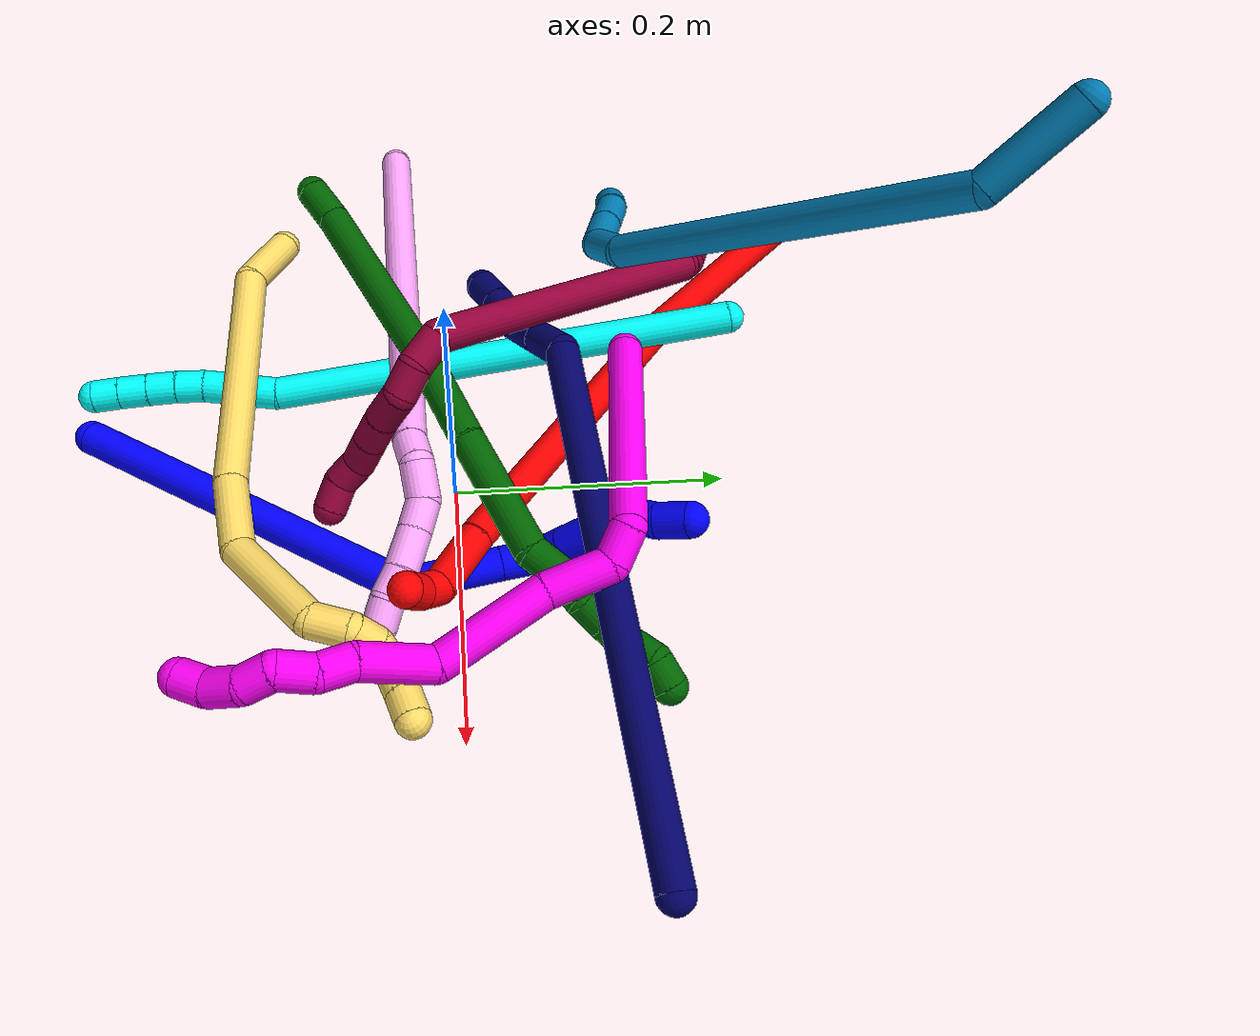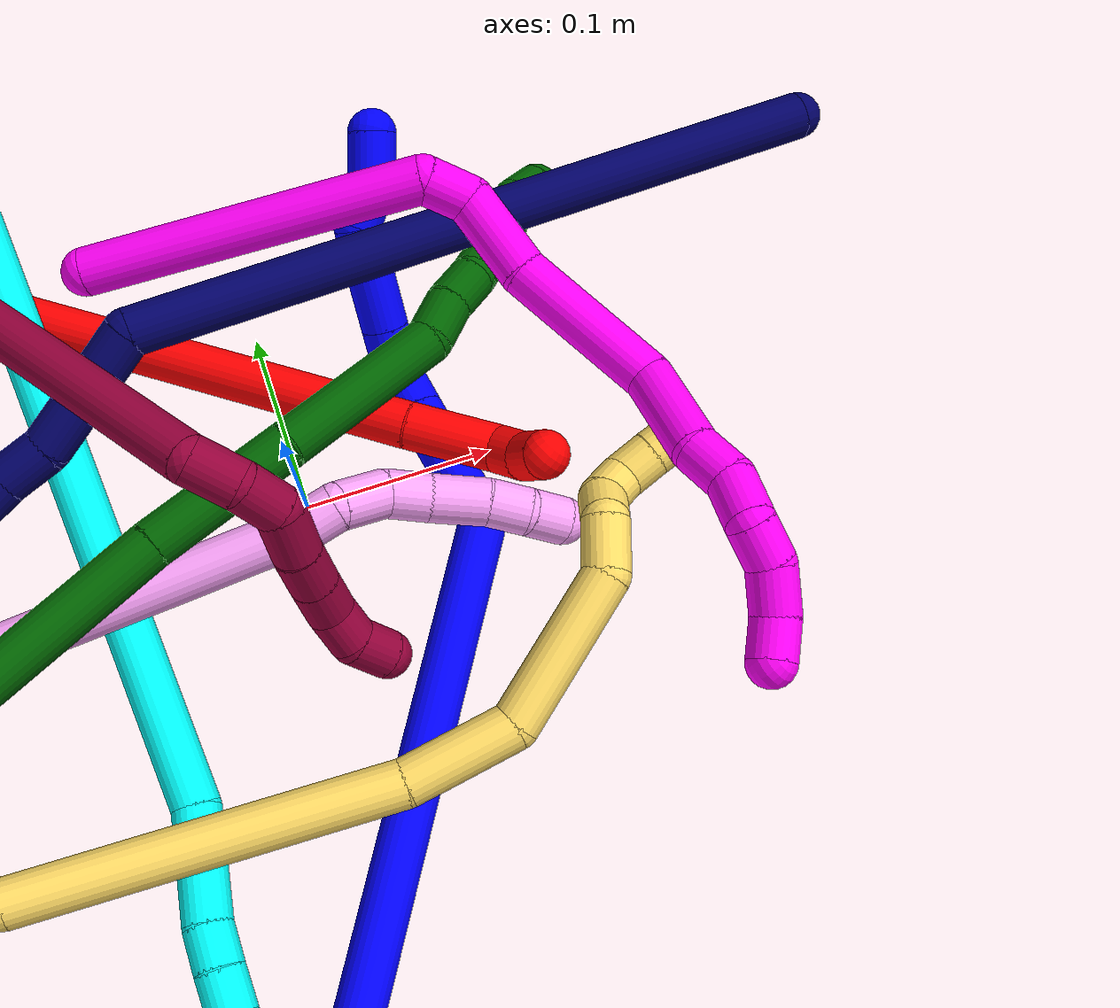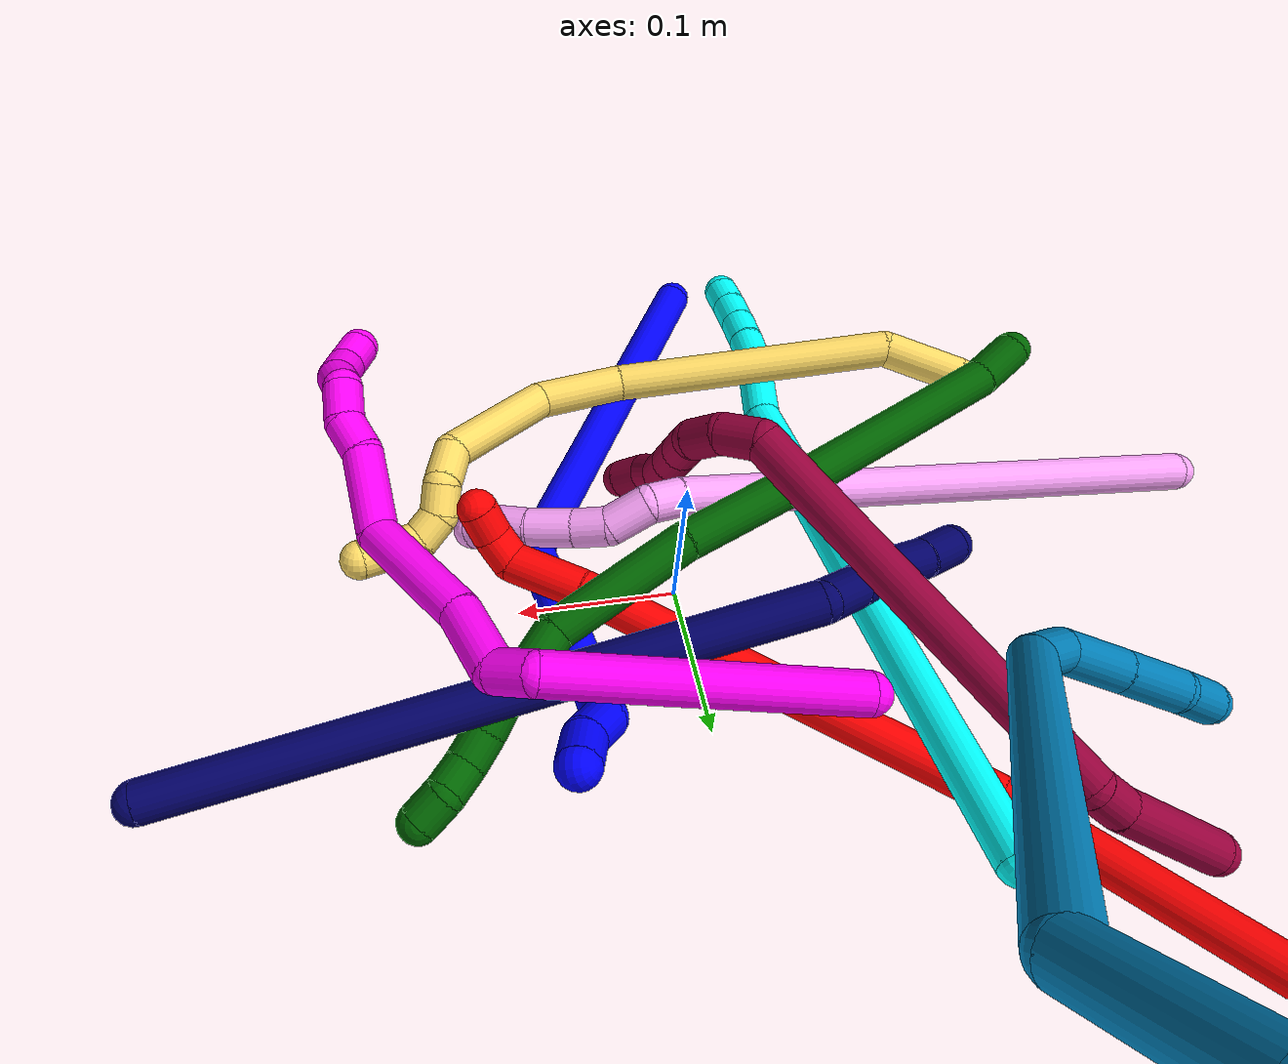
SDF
<sdf version="1.7">
 <world name="default">
  <plugin name="TubeGeneratorPlugin" filename="libtube_generator_plugin.so"/>
  <model name="photoneo_s_sensor">
   <static>1</static>
   <pose>0 0 2 1.57079 1.57079 3.14159</pose>
   <link name="link">
    <inertial><mass>0.1</mass></inertial>
    <sensor name="sensor" type="depth">
     <update_rate>30</update_rate>
     <camera>
      <horizontal_fov>1.22</horizontal_fov>
      <image><width>1920</width><height>1200</height><format>B8G8R8</format></image>
      <clip><near>0.1</near><far>4</far></clip>
      <depth_camera><output>points</output></depth_camera>
     </camera>
     <plugin name="camera_plugin" filename="libgazebo_ros_depth_camera.so">
      <baseline>0.2</baseline>
      <alwaysOn>1</alwaysOn>
      <updateRate>0.0</updateRate>
      <cameraName>camera_ir</cameraName>
      <imageTopicName>/camera/color/image_raw</imageTopicName>
      <cameraInfoTopicName>/camera/color/camera_info</cameraInfoTopicName>
      <depthImageTopicName>/camera/depth/image_raw</depthImageTopicName>
      <depthImageCameraInfoTopicName>/camera/depth/camera_info</depthImageCameraInfoTopicName>
      <pointCloudTopicName>/camera/depth/points</pointCloudTopicName>
      <frameName>fr_optical</frameName>
      <pointCloudCutoff>0.1</pointCloudCutoff>
      <pointCloudCutoffMax>2.0</pointCloudCutoffMax>
      <distortionK1>0</distortionK1>
      <distortionK2>0</distortionK2>
      <distortionK3>0</distortionK3>
      <distortionT1>0</distortionT1>
      <distortionT2>0</distortionT2>
      <CxPrime>0</CxPrime>
      <Cx>0</Cx>
      <Cy>0</Cy>
      <focalLength>0</focalLength>
      <hackBaseline>0</hackBaseline>
     </plugin>
    </sensor>
   </link>
  </model>
  <gravity>0 0 -9.8</gravity>
  <magnetic_field>6e-06 2.3e-05 -4.2e-05</magnetic_field>
  <atmosphere type="adiabatic"/>
  <physics name="default_physics" default="0" type="ode">
   <max_step_size>0.003</max_step_size>
   <real_time_factor>1</real_time_factor>
   <real_time_update_rate>1000</real_time_update_rate>
   <max_contacts>10000</max_contacts>
   <ode>
    <solver>
     <type>quick</type>
     <iters>100</iters>
     <sor>1.3</sor>
     <use_dynamic_moi_rescaling>0</use_dynamic_moi_rescaling>
    </solver>
    <constraints>
     <contact_max_correcting_vel>0</contact_max_correcting_vel>
     <contact_surface_layer>0.001</contact_surface_layer>
     <cfm>0</cfm>
     <erp>0.2</erp>
    </constraints>
   </ode>
  </physics>
  <scene><ambient>0.4 0.4 0.4 1</ambient><background>0.7 0.7 0.7 1</background><shadows>0</shadows></scene>
  <audio><device>default</device></audio>
  <spherical_coordinates>
   <surface_model>EARTH_WGS84</surface_model>
   <latitude_deg>0</latitude_deg>
   <longitude_deg>0</longitude_deg>
   <elevation>0</elevation>
   <heading_deg>0</heading_deg>
  </spherical_coordinates>
  <model name="bin">
   <static>1</static>
   <link name="bottom">
    <collision name="collision-bottom">
     <pose>0 0 -0.01 0 -0 0</pose>
     <geometry><box><size>0.8 0.6 0.02</size></box></geometry>
     <surface>
      <friction><ode><mu>100</mu><mu2>100</mu2></ode></friction>
      <contact><collide_bitmask>65535</collide_bitmask></contact>
     </surface>
    </collision>
   </link>
   <link name="west_wall">
    <collision name="collision-west_wall">
     <pose>-0.41 0 0.1 0 -0 0</pose>
     <geometry><box><size>0.02 0.6 0.2</size></box></geometry>
     <surface>
      <friction><ode><mu>100</mu><mu2>100</mu2></ode></friction>
      <contact><collide_bitmask>65535</collide_bitmask></contact>
     </surface>
    </collision>
   </link>
   <link name="east_wall">
    <collision name="collision-east_wall">
     <pose>0.41 0 0.1 0 -0 0</pose>
     <geometry><box><size>0.02 0.6 0.2</size></box></geometry>
     <surface>
      <friction><ode><mu>100</mu><mu2>100</mu2></ode></friction>
      <contact><collide_bitmask>65535</collide_bitmask></contact>
     </surface>
    </collision>
   </link>
   <link name="south_wall">
    <collision name="collision-south_wall">
     <pose>0 -0.31 0.1 0 -0 0</pose>
     <geometry><box><size>0.8 0.02 0.2</size></box></geometry>
     <surface>
      <friction><ode><mu>100</mu><mu2>100</mu2></ode></friction>
      <contact><collide_bitmask>65535</collide_bitmask></contact>
     </surface>
    </collision>
   </link>
   <link name="north_wall">
    <collision name="collision-north_wall">
     <pose>0 0.31 0.1 0 -0 0</pose>
     <geometry><box><size>0.8 0.02 0.2</size></box></geometry>
     <surface>
      <friction><ode><mu>100</mu><mu2>100</mu2></ode></friction>
      <contact><collide_bitmask>65535</collide_bitmask></contact>
     </surface>
    </collision>
   </link>
  </model>
  <model name="1">
   <static>0</static>
   <link name="1">
    <collision name="collision-cylinder-e_1_1_4">
     <pose>0.057742 0.122794 -0.021496 -1.7441 0.433771 -0.512999</pose>
     <geometry><cylinder><radius>0.0125</radius><length>0.27477</length></cylinder></geometry>
     <surface>
      <friction><ode><mu>1.16</mu><mu2>1.16</mu2><slip1>0</slip1><slip2>0</slip2></ode></friction>
      <contact><ode><kp>1e+06</kp><kd>1</kd><max_vel>0</max_vel><min_depth>0.001</min_depth></ode></contact>
     </surface>
    </collision>
    <visual name="visual-cylinder-e_1_1_4">
     <pose>0.057742 0.122794 -0.021496 -1.7441 0.433771 -0.512999</pose>
     <geometry><cylinder><radius>0.0125</radius><length>0.27477</length></cylinder></geometry>
     <material><ambient>0 0 1 1</ambient></material>
    </visual>
    <collision name="collision-cylinder-e_2_4_5">
     <pose>0.117115 0.276968 -0.026891 -1.09671 0.046194 -0.028221</pose>
     <geometry><cylinder><radius>0.0125</radius><length>0.070616</length></cylinder></geometry>
     <surface>
      <friction><ode><mu>1.16</mu><mu2>1.16</mu2><slip1>0</slip1><slip2>0</slip2></ode></friction>
      <contact><ode><kp>1e+06</kp><kd>1</kd><max_vel>0</max_vel><min_depth>0.001</min_depth></ode></contact>
     </surface>
    </collision>
    <visual name="visual-cylinder-e_2_4_5">
     <pose>0.117115 0.276968 -0.026891 -1.09671 0.046194 -0.028221</pose>
     <geometry><cylinder><radius>0.0125</radius><length>0.070616</length></cylinder></geometry>
     <material><ambient>0 0 1 1</ambient></material>
    </visual>
    <collision name="collision-cylinder-e_3_5_6">
     <pose>0.11921 0.320253 -0.005001 -1.11822 0.0351 -0.021964</pose>
     <geometry><cylinder><radius>0.0125</radius><length>0.02649</length></cylinder></geometry>
     <surface>
      <friction><ode><mu>1.16</mu><mu2>1.16</mu2><slip1>0</slip1><slip2>0</slip2></ode></friction>
      <contact><ode><kp>1e+06</kp><kd>1</kd><max_vel>0</max_vel><min_depth>0.001</min_depth></ode></contact>
     </surface>
    </collision>
    <visual name="visual-cylinder-e_3_5_6">
     <pose>0.11921 0.320253 -0.005001 -1.11822 0.0351 -0.021964</pose>
     <geometry><cylinder><radius>0.0125</radius><length>0.02649</length></cylinder></geometry>
     <material><ambient>0 0 1 1</ambient></material>
    </visual>
    <collision name="collision-cylinder-e_4_6_7">
     <pose>0.127375 0.338675 0.007436 -0.775483 0.690956 -0.291898</pose>
     <geometry><cylinder><radius>0.0125</radius><length>0.024164</length></cylinder></geometry>
     <surface>
      <friction><ode><mu>1.16</mu><mu2>1.16</mu2><slip1>0</slip1><slip2>0</slip2></ode></friction>
      <contact><ode><kp>1e+06</kp><kd>1</kd><max_vel>0</max_vel><min_depth>0.001</min_depth></ode></contact>
     </surface>
    </collision>
    <visual name="visual-cylinder-e_4_6_7">
     <pose>0.127375 0.338675 0.007436 -0.775483 0.690956 -0.291898</pose>
     <geometry><cylinder><radius>0.0125</radius><length>0.024164</length></cylinder></geometry>
     <material><ambient>0 0 1 1</ambient></material>
    </visual>
    <collision name="collision-cylinder-e_5_7_8">
     <pose>0.152674 0.360296 0.029231 -0.783962 0.688529 -0.294281</pose>
     <geometry><cylinder><radius>0.0125</radius><length>0.055399</length></cylinder></geometry>
     <surface>
      <friction><ode><mu>1.16</mu><mu2>1.16</mu2><slip1>0</slip1><slip2>0</slip2></ode></friction>
      <contact><ode><kp>1e+06</kp><kd>1</kd><max_vel>0</max_vel><min_depth>0.001</min_depth></ode></contact>
     </surface>
    </collision>
    <visual name="visual-cylinder-e_5_7_8">
     <pose>0.152674 0.360296 0.029231 -0.783962 0.688529 -0.294281</pose>
     <geometry><cylinder><radius>0.0125</radius><length>0.055399</length></cylinder></geometry>
     <material><ambient>0 0 1 1</ambient></material>
    </visual>
    <collision name="collision-cylinder-e_6_8_9">
     <pose>0.180566 0.38273 0.044424 -1.56441 0.951799 -0.94661</pose>
     <geometry><cylinder><radius>0.0125</radius><length>0.025273</length></cylinder></geometry>
     <surface>
      <friction><ode><mu>1.16</mu><mu2>1.16</mu2><slip1>0</slip1><slip2>0</slip2></ode></friction>
      <contact><ode><kp>1e+06</kp><kd>1</kd><max_vel>0</max_vel><min_depth>0.001</min_depth></ode></contact>
     </surface>
    </collision>
    <visual name="visual-cylinder-e_6_8_9">
     <pose>0.180566 0.38273 0.044424 -1.56441 0.951799 -0.94661</pose>
     <geometry><cylinder><radius>0.0125</radius><length>0.025273</length></cylinder></geometry>
     <material><ambient>0 0 1 1</ambient></material>
    </visual>
    <collision name="collision-cylinder-e_7_9_2">
     <pose>0.198121 0.39868 0.0474 -1.24308 0.67344 -0.49131</pose>
     <geometry><cylinder><radius>0.0125</radius><length>0.023289</length></cylinder></geometry>
     <surface>
      <friction><ode><mu>1.16</mu><mu2>1.16</mu2><slip1>0</slip1><slip2>0</slip2></ode></friction>
      <contact><ode><kp>1e+06</kp><kd>1</kd><max_vel>0</max_vel><min_depth>0.001</min_depth></ode></contact>
     </surface>
    </collision>
    <visual name="visual-cylinder-e_7_9_2">
     <pose>0.198121 0.39868 0.0474 -1.24308 0.67344 -0.49131</pose>
     <geometry><cylinder><radius>0.0125</radius><length>0.023289</length></cylinder></geometry>
     <material><ambient>0 0 1 1</ambient></material>
    </visual>
    <collision name="collision-sphere-2">
     <pose>0.205383 0.407297 0.05033 0 -0 0</pose>
     <geometry><sphere><radius>0.0125</radius></sphere></geometry>
     <surface>
      <friction><ode><mu>1.16</mu><mu2>1.16</mu2><slip1>0</slip1><slip2>0</slip2></ode></friction>
      <contact><ode><kp>1e+06</kp><kd>1</kd><max_vel>0</max_vel><min_depth>0.001</min_depth></ode></contact>
     </surface>
    </collision>
    <visual name="visual-sphere-2">
     <pose>0.205383 0.407297 0.05033 0 -0 0</pose>
     <geometry><sphere><radius>0.0125</radius></sphere></geometry>
     <material><ambient>0 0 1 1</ambient></material>
    </visual>
    <collision name="collision-sphere-9">
     <pose>0.190858 0.390062 0.044471 0 -0 0</pose>
     <geometry><sphere><radius>0.0125</radius></sphere></geometry>
     <surface>
      <friction><ode><mu>1.16</mu><mu2>1.16</mu2><slip1>0</slip1><slip2>0</slip2></ode></friction>
      <contact><ode><kp>1e+06</kp><kd>1</kd><max_vel>0</max_vel><min_depth>0.001</min_depth></ode></contact>
     </surface>
    </collision>
    <visual name="visual-sphere-9">
     <pose>0.190858 0.390062 0.044471 0 -0 0</pose>
     <geometry><sphere><radius>0.0125</radius></sphere></geometry>
     <material><ambient>0 0 1 1</ambient></material>
    </visual>
    <collision name="collision-sphere-4">
     <pose>0.115484 0.245588 -0.042992 0 -0 0</pose>
     <geometry><sphere><radius>0.0125</radius></sphere></geometry>
     <surface>
      <friction><ode><mu>1.16</mu><mu2>1.16</mu2><slip1>0</slip1><slip2>0</slip2></ode></friction>
      <contact><ode><kp>1e+06</kp><kd>1</kd><max_vel>0</max_vel><min_depth>0.001</min_depth></ode></contact>
     </surface>
    </collision>
    <visual name="visual-sphere-4">
     <pose>0.115484 0.245588 -0.042992 0 -0 0</pose>
     <geometry><sphere><radius>0.0125</radius></sphere></geometry>
     <material><ambient>0 0 1 1</ambient></material>
    </visual>
    <collision name="collision-sphere-1">
     <geometry><sphere><radius>0.0125</radius></sphere></geometry>
     <surface>
      <friction><ode><mu>1.16</mu><mu2>1.16</mu2><slip1>0</slip1><slip2>0</slip2></ode></friction>
      <contact><ode><kp>1e+06</kp><kd>1</kd><max_vel>0</max_vel><min_depth>0.001</min_depth></ode></contact>
     </surface>
    </collision>
    <visual name="visual-sphere-1">
     <geometry><sphere><radius>0.0125</radius></sphere></geometry>
     <material><ambient>0 0 1 1</ambient></material>
    </visual>
    <collision name="collision-sphere-8">
     <pose>0.170275 0.375399 0.044377 0 -0 0</pose>
     <geometry><sphere><radius>0.0125</radius></sphere></geometry>
     <surface>
      <friction><ode><mu>1.16</mu><mu2>1.16</mu2><slip1>0</slip1><slip2>0</slip2></ode></friction>
      <contact><ode><kp>1e+06</kp><kd>1</kd><max_vel>0</max_vel><min_depth>0.001</min_depth></ode></contact>
     </surface>
    </collision>
    <visual name="visual-sphere-8">
     <pose>0.170275 0.375399 0.044377 0 -0 0</pose>
     <geometry><sphere><radius>0.0125</radius></sphere></geometry>
     <material><ambient>0 0 1 1</ambient></material>
    </visual>
    <collision name="collision-sphere-5">
     <pose>0.118745 0.308349 -0.010789 0 -0 0</pose>
     <geometry><sphere><radius>0.0125</radius></sphere></geometry>
     <surface>
      <friction><ode><mu>1.16</mu><mu2>1.16</mu2><slip1>0</slip1><slip2>0</slip2></ode></friction>
      <contact><ode><kp>1e+06</kp><kd>1</kd><max_vel>0</max_vel><min_depth>0.001</min_depth></ode></contact>
     </surface>
    </collision>
    <visual name="visual-sphere-5">
     <pose>0.118745 0.308349 -0.010789 0 -0 0</pose>
     <geometry><sphere><radius>0.0125</radius></sphere></geometry>
     <material><ambient>0 0 1 1</ambient></material>
    </visual>
    <collision name="collision-sphere-6">
     <pose>0.119675 0.332157 0.000788 0 -0 0</pose>
     <geometry><sphere><radius>0.0125</radius></sphere></geometry>
     <surface>
      <friction><ode><mu>1.16</mu><mu2>1.16</mu2><slip1>0</slip1><slip2>0</slip2></ode></friction>
      <contact><ode><kp>1e+06</kp><kd>1</kd><max_vel>0</max_vel><min_depth>0.001</min_depth></ode></contact>
     </surface>
    </collision>
    <visual name="visual-sphere-6">
     <pose>0.119675 0.332157 0.000788 0 -0 0</pose>
     <geometry><sphere><radius>0.0125</radius></sphere></geometry>
     <material><ambient>0 0 1 1</ambient></material>
    </visual>
    <collision name="collision-sphere-7">
     <pose>0.135074 0.345194 0.014085 0 -0 0</pose>
     <geometry><sphere><radius>0.0125</radius></sphere></geometry>
     <surface>
      <friction><ode><mu>1.16</mu><mu2>1.16</mu2><slip1>0</slip1><slip2>0</slip2></ode></friction>
      <contact><ode><kp>1e+06</kp><kd>1</kd><max_vel>0</max_vel><min_depth>0.001</min_depth></ode></contact>
     </surface>
    </collision>
    <visual name="visual-sphere-7">
     <pose>0.135074 0.345194 0.014085 0 -0 0</pose>
     <geometry><sphere><radius>0.0125</radius></sphere></geometry>
     <material><ambient>0 0 1 1</ambient></material>
    </visual>
    <inertial>
     <pose>0.096014 0.217766 -0.007824 0 -0 0</pose>
     <mass>0.5</mass>
     <inertia>
      <ixx>0.00066</ixx>
      <ixy>0</ixy>
      <ixz>0</ixz>
      <iyy>-0.000624</iyy>
      <iyz>0</iyz>
      <izz>-0.002342</izz>
     </inertia>
    </inertial>
   </link>
   <pose>-0.059805 -0.274001 0.012836 -0.520588 -0.937129 0.247189</pose>
  </model>
  <model name="2">
   <static>0</static>
   <link name="2">
    <collision name="collision-cylinder-e_1_1_4">
     <pose>0.017638 -0.072492 -0.015731 1.78449 0.233444 0.288835</pose>
     <geometry><cylinder><radius>0.0125</radius><length>0.152494</length></cylinder></geometry>
     <surface>
      <friction><ode><mu>1.16</mu><mu2>1.16</mu2><slip1>0</slip1><slip2>0</slip2></ode></friction>
      <contact><ode><kp>1e+06</kp><kd>1</kd><max_vel>0</max_vel><min_depth>0.001</min_depth></ode></contact>
     </surface>
    </collision>
    <visual name="visual-cylinder-e_1_1_4">
     <pose>0.017638 -0.072492 -0.015731 1.78449 0.233444 0.288835</pose>
     <geometry><cylinder><radius>0.0125</radius><length>0.152494</length></cylinder></geometry>
     <material><ambient>1 0 0 1</ambient></material>
    </visual>
    <collision name="collision-cylinder-e_2_4_5">
     <pose>0.066744 -0.254284 -0.093523 2.08719 0.245312 0.417342</pose>
     <geometry><cylinder><radius>0.0125</radius><length>0.25914</length></cylinder></geometry>
     <surface>
      <friction><ode><mu>1.16</mu><mu2>1.16</mu2><slip1>0</slip1><slip2>0</slip2></ode></friction>
      <contact><ode><kp>1e+06</kp><kd>1</kd><max_vel>0</max_vel><min_depth>0.001</min_depth></ode></contact>
     </surface>
    </collision>
    <visual name="visual-cylinder-e_2_4_5">
     <pose>0.066744 -0.254284 -0.093523 2.08719 0.245312 0.417342</pose>
     <geometry><cylinder><radius>0.0125</radius><length>0.25914</length></cylinder></geometry>
     <material><ambient>1 0 0 1</ambient></material>
    </visual>
    <collision name="collision-cylinder-e_3_5_6">
     <pose>0.101898 -0.384398 -0.166992 2.07224 0.154128 0.25931</pose>
     <geometry><cylinder><radius>0.0125</radius><length>0.048039</length></cylinder></geometry>
     <surface>
      <friction><ode><mu>1.16</mu><mu2>1.16</mu2><slip1>0</slip1><slip2>0</slip2></ode></friction>
      <contact><ode><kp>1e+06</kp><kd>1</kd><max_vel>0</max_vel><min_depth>0.001</min_depth></ode></contact>
     </surface>
    </collision>
    <visual name="visual-cylinder-e_3_5_6">
     <pose>0.101898 -0.384398 -0.166992 2.07224 0.154128 0.25931</pose>
     <geometry><cylinder><radius>0.0125</radius><length>0.048039</length></cylinder></geometry>
     <material><ambient>1 0 0 1</ambient></material>
    </visual>
    <collision name="collision-cylinder-e_4_6_7">
     <pose>0.112814 -0.410146 -0.183357 2.3583 0.801827 1.59682</pose>
     <geometry><cylinder><radius>0.0125</radius><length>0.020117</length></cylinder></geometry>
     <surface>
      <friction><ode><mu>1.16</mu><mu2>1.16</mu2><slip1>0</slip1><slip2>0</slip2></ode></friction>
      <contact><ode><kp>1e+06</kp><kd>1</kd><max_vel>0</max_vel><min_depth>0.001</min_depth></ode></contact>
     </surface>
    </collision>
    <visual name="visual-cylinder-e_4_6_7">
     <pose>0.112814 -0.410146 -0.183357 2.3583 0.801827 1.59682</pose>
     <geometry><cylinder><radius>0.0125</radius><length>0.020117</length></cylinder></geometry>
     <material><ambient>1 0 0 1</ambient></material>
    </visual>
    <collision name="collision-cylinder-e_5_7_2">
     <pose>0.128045 -0.416772 -0.194248 2.86421 0.913963 2.58837</pose>
     <geometry><cylinder><radius>0.0125</radius><length>0.02021</length></cylinder></geometry>
     <surface>
      <friction><ode><mu>1.16</mu><mu2>1.16</mu2><slip1>0</slip1><slip2>0</slip2></ode></friction>
      <contact><ode><kp>1e+06</kp><kd>1</kd><max_vel>0</max_vel><min_depth>0.001</min_depth></ode></contact>
     </surface>
    </collision>
    <visual name="visual-cylinder-e_5_7_2">
     <pose>0.128045 -0.416772 -0.194248 2.86421 0.913963 2.58837</pose>
     <geometry><cylinder><radius>0.0125</radius><length>0.02021</length></cylinder></geometry>
     <material><ambient>1 0 0 1</ambient></material>
    </visual>
    <collision name="collision-sphere-2">
     <pose>0.136047 -0.418461 -0.200183 0 -0 0</pose>
     <geometry><sphere><radius>0.0125</radius></sphere></geometry>
     <surface>
      <friction><ode><mu>1.16</mu><mu2>1.16</mu2><slip1>0</slip1><slip2>0</slip2></ode></friction>
      <contact><ode><kp>1e+06</kp><kd>1</kd><max_vel>0</max_vel><min_depth>0.001</min_depth></ode></contact>
     </surface>
    </collision>
    <visual name="visual-sphere-2">
     <pose>0.136047 -0.418461 -0.200183 0 -0 0</pose>
     <geometry><sphere><radius>0.0125</radius></sphere></geometry>
     <material><ambient>1 0 0 1</ambient></material>
    </visual>
    <collision name="collision-sphere-7">
     <pose>0.120042 -0.415082 -0.188314 0 -0 0</pose>
     <geometry><sphere><radius>0.0125</radius></sphere></geometry>
     <surface>
      <friction><ode><mu>1.16</mu><mu2>1.16</mu2><slip1>0</slip1><slip2>0</slip2></ode></friction>
      <contact><ode><kp>1e+06</kp><kd>1</kd><max_vel>0</max_vel><min_depth>0.001</min_depth></ode></contact>
     </surface>
    </collision>
    <visual name="visual-sphere-7">
     <pose>0.120042 -0.415082 -0.188314 0 -0 0</pose>
     <geometry><sphere><radius>0.0125</radius></sphere></geometry>
     <material><ambient>1 0 0 1</ambient></material>
    </visual>
    <collision name="collision-sphere-6">
     <pose>0.105586 -0.405211 -0.178401 0 -0 0</pose>
     <geometry><sphere><radius>0.0125</radius></sphere></geometry>
     <surface>
      <friction><ode><mu>1.16</mu><mu2>1.16</mu2><slip1>0</slip1><slip2>0</slip2></ode></friction>
      <contact><ode><kp>1e+06</kp><kd>1</kd><max_vel>0</max_vel><min_depth>0.001</min_depth></ode></contact>
     </surface>
    </collision>
    <visual name="visual-sphere-6">
     <pose>0.105586 -0.405211 -0.178401 0 -0 0</pose>
     <geometry><sphere><radius>0.0125</radius></sphere></geometry>
     <material><ambient>1 0 0 1</ambient></material>
    </visual>
    <collision name="collision-sphere-5">
     <pose>0.098211 -0.363585 -0.155583 0 -0 0</pose>
     <geometry><sphere><radius>0.0125</radius></sphere></geometry>
     <surface>
      <friction><ode><mu>1.16</mu><mu2>1.16</mu2><slip1>0</slip1><slip2>0</slip2></ode></friction>
      <contact><ode><kp>1e+06</kp><kd>1</kd><max_vel>0</max_vel><min_depth>0.001</min_depth></ode></contact>
     </surface>
    </collision>
    <visual name="visual-sphere-5">
     <pose>0.098211 -0.363585 -0.155583 0 -0 0</pose>
     <geometry><sphere><radius>0.0125</radius></sphere></geometry>
     <material><ambient>1 0 0 1</ambient></material>
    </visual>
    <collision name="collision-sphere-1">
     <geometry><sphere><radius>0.0125</radius></sphere></geometry>
     <surface>
      <friction><ode><mu>1.16</mu><mu2>1.16</mu2><slip1>0</slip1><slip2>0</slip2></ode></friction>
      <contact><ode><kp>1e+06</kp><kd>1</kd><max_vel>0</max_vel><min_depth>0.001</min_depth></ode></contact>
     </surface>
    </collision>
    <visual name="visual-sphere-1">
     <geometry><sphere><radius>0.0125</radius></sphere></geometry>
     <material><ambient>1 0 0 1</ambient></material>
    </visual>
    <collision name="collision-sphere-4">
     <pose>0.035276 -0.144983 -0.031463 0 -0 0</pose>
     <geometry><sphere><radius>0.0125</radius></sphere></geometry>
     <surface>
      <friction><ode><mu>1.16</mu><mu2>1.16</mu2><slip1>0</slip1><slip2>0</slip2></ode></friction>
      <contact><ode><kp>1e+06</kp><kd>1</kd><max_vel>0</max_vel><min_depth>0.001</min_depth></ode></contact>
     </surface>
    </collision>
    <visual name="visual-sphere-4">
     <pose>0.035276 -0.144983 -0.031463 0 -0 0</pose>
     <geometry><sphere><radius>0.0125</radius></sphere></geometry>
     <material><ambient>1 0 0 1</ambient></material>
    </visual>
    <inertial>
     <pose>0.059476 -0.224179 -0.084542 0 -0 0</pose>
     <mass>0.5</mass>
     <inertia>
      <ixx>0.002259</ixx>
      <ixy>0</ixy>
      <ixz>0</ixz>
      <iyy>5.1e-05</iyy>
      <iyz>0</iyz>
      <izz>0.001085</izz>
     </inertia>
    </inertial>
   </link>
   <pose>-0.241098 0.285272 0.025758 2.47153 -0.882997 -1.94375</pose>
  </model>
  <model name="3">
   <static>0</static>
   <link name="3">
    <collision name="collision-cylinder-e_1_1_4">
     <pose>0.024245 -0.174225 -0.030075 1.74173 0.136283 0.161721</pose>
     <geometry><cylinder><radius>0.0125</radius><length>0.356913</length></cylinder></geometry>
     <surface>
      <friction><ode><mu>1.16</mu><mu2>1.16</mu2><slip1>0</slip1><slip2>0</slip2></ode></friction>
      <contact><ode><kp>1e+06</kp><kd>1</kd><max_vel>0</max_vel><min_depth>0.001</min_depth></ode></contact>
     </surface>
    </collision>
    <visual name="visual-cylinder-e_1_1_4">
     <pose>0.024245 -0.174225 -0.030075 1.74173 0.136283 0.161721</pose>
     <geometry><cylinder><radius>0.0125</radius><length>0.356913</length></cylinder></geometry>
     <material><ambient>0.003922 1 0.996078 1</ambient></material>
    </visual>
    <collision name="collision-cylinder-e_2_4_5">
     <pose>0.046368 -0.376927 -0.060038 1.56688 -0.074412 -0.074122</pose>
     <geometry><cylinder><radius>0.0125</radius><length>0.057112</length></cylinder></geometry>
     <surface>
      <friction><ode><mu>1.16</mu><mu2>1.16</mu2><slip1>0</slip1><slip2>0</slip2></ode></friction>
      <contact><ode><kp>1e+06</kp><kd>1</kd><max_vel>0</max_vel><min_depth>0.001</min_depth></ode></contact>
     </surface>
    </collision>
    <visual name="visual-cylinder-e_2_4_5">
     <pose>0.046368 -0.376927 -0.060038 1.56688 -0.074412 -0.074122</pose>
     <geometry><cylinder><radius>0.0125</radius><length>0.057112</length></cylinder></geometry>
     <material><ambient>0.003922 1 0.996078 1</ambient></material>
    </visual>
    <collision name="collision-cylinder-e_3_5_6">
     <pose>0.04512 -0.416145 -0.060348 1.61 0.081192 0.084436</pose>
     <geometry><cylinder><radius>0.0125</radius><length>0.021571</length></cylinder></geometry>
     <surface>
      <friction><ode><mu>1.16</mu><mu2>1.16</mu2><slip1>0</slip1><slip2>0</slip2></ode></friction>
      <contact><ode><kp>1e+06</kp><kd>1</kd><max_vel>0</max_vel><min_depth>0.001</min_depth></ode></contact>
     </surface>
    </collision>
    <visual name="visual-cylinder-e_3_5_6">
     <pose>0.04512 -0.416145 -0.060348 1.61 0.081192 0.084436</pose>
     <geometry><cylinder><radius>0.0125</radius><length>0.021571</length></cylinder></geometry>
     <material><ambient>0.003922 1 0.996078 1</ambient></material>
    </visual>
    <collision name="collision-cylinder-e_4_6_7">
     <pose>0.046984 -0.437783 -0.062034 1.68635 0.089986 0.101017</pose>
     <geometry><cylinder><radius>0.0125</radius><length>0.022029</length></cylinder></geometry>
     <surface>
      <friction><ode><mu>1.16</mu><mu2>1.16</mu2><slip1>0</slip1><slip2>0</slip2></ode></friction>
      <contact><ode><kp>1e+06</kp><kd>1</kd><max_vel>0</max_vel><min_depth>0.001</min_depth></ode></contact>
     </surface>
    </collision>
    <visual name="visual-cylinder-e_4_6_7">
     <pose>0.046984 -0.437783 -0.062034 1.68635 0.089986 0.101017</pose>
     <geometry><cylinder><radius>0.0125</radius><length>0.022029</length></cylinder></geometry>
     <material><ambient>0.003922 1 0.996078 1</ambient></material>
    </visual>
    <collision name="collision-cylinder-e_5_7_8">
     <pose>0.049238 -0.459527 -0.06457 1.6875 0.115217 0.129475</pose>
     <geometry><cylinder><radius>0.0125</radius><length>0.021989</length></cylinder></geometry>
     <surface>
      <friction><ode><mu>1.16</mu><mu2>1.16</mu2><slip1>0</slip1><slip2>0</slip2></ode></friction>
      <contact><ode><kp>1e+06</kp><kd>1</kd><max_vel>0</max_vel><min_depth>0.001</min_depth></ode></contact>
     </surface>
    </collision>
    <visual name="visual-cylinder-e_5_7_8">
     <pose>0.049238 -0.459527 -0.06457 1.6875 0.115217 0.129475</pose>
     <geometry><cylinder><radius>0.0125</radius><length>0.021989</length></cylinder></geometry>
     <material><ambient>0.003922 1 0.996078 1</ambient></material>
    </visual>
    <collision name="collision-cylinder-e_6_8_2">
     <pose>0.05176 -0.480381 -0.067325 1.71794 0.123743 0.143373</pose>
     <geometry><cylinder><radius>0.0125</radius><length>0.020387</length></cylinder></geometry>
     <surface>
      <friction><ode><mu>1.16</mu><mu2>1.16</mu2><slip1>0</slip1><slip2>0</slip2></ode></friction>
      <contact><ode><kp>1e+06</kp><kd>1</kd><max_vel>0</max_vel><min_depth>0.001</min_depth></ode></contact>
     </surface>
    </collision>
    <visual name="visual-cylinder-e_6_8_2">
     <pose>0.05176 -0.480381 -0.067325 1.71794 0.123743 0.143373</pose>
     <geometry><cylinder><radius>0.0125</radius><length>0.020387</length></cylinder></geometry>
     <material><ambient>0.003922 1 0.996078 1</ambient></material>
    </visual>
    <collision name="collision-sphere-2">
     <pose>0.053018 -0.490387 -0.068808 0 -0 0</pose>
     <geometry><sphere><radius>0.0125</radius></sphere></geometry>
     <surface>
      <friction><ode><mu>1.16</mu><mu2>1.16</mu2><slip1>0</slip1><slip2>0</slip2></ode></friction>
      <contact><ode><kp>1e+06</kp><kd>1</kd><max_vel>0</max_vel><min_depth>0.001</min_depth></ode></contact>
     </surface>
    </collision>
    <visual name="visual-sphere-2">
     <pose>0.053018 -0.490387 -0.068808 0 -0 0</pose>
     <geometry><sphere><radius>0.0125</radius></sphere></geometry>
     <material><ambient>0.003922 1 0.996078 1</ambient></material>
    </visual>
    <collision name="collision-sphere-4">
     <pose>0.048491 -0.34845 -0.060149 0 -0 0</pose>
     <geometry><sphere><radius>0.0125</radius></sphere></geometry>
     <surface>
      <friction><ode><mu>1.16</mu><mu2>1.16</mu2><slip1>0</slip1><slip2>0</slip2></ode></friction>
      <contact><ode><kp>1e+06</kp><kd>1</kd><max_vel>0</max_vel><min_depth>0.001</min_depth></ode></contact>
     </surface>
    </collision>
    <visual name="visual-sphere-4">
     <pose>0.048491 -0.34845 -0.060149 0 -0 0</pose>
     <geometry><sphere><radius>0.0125</radius></sphere></geometry>
     <material><ambient>0.003922 1 0.996078 1</ambient></material>
    </visual>
    <collision name="collision-sphere-1">
     <geometry><sphere><radius>0.0125</radius></sphere></geometry>
     <surface>
      <friction><ode><mu>1.16</mu><mu2>1.16</mu2><slip1>0</slip1><slip2>0</slip2></ode></friction>
      <contact><ode><kp>1e+06</kp><kd>1</kd><max_vel>0</max_vel><min_depth>0.001</min_depth></ode></contact>
     </surface>
    </collision>
    <visual name="visual-sphere-1">
     <geometry><sphere><radius>0.0125</radius></sphere></geometry>
     <material><ambient>0.003922 1 0.996078 1</ambient></material>
    </visual>
    <collision name="collision-sphere-8">
     <pose>0.050502 -0.470375 -0.065842 0 -0 0</pose>
     <geometry><sphere><radius>0.0125</radius></sphere></geometry>
     <surface>
      <friction><ode><mu>1.16</mu><mu2>1.16</mu2><slip1>0</slip1><slip2>0</slip2></ode></friction>
      <contact><ode><kp>1e+06</kp><kd>1</kd><max_vel>0</max_vel><min_depth>0.001</min_depth></ode></contact>
     </surface>
    </collision>
    <visual name="visual-sphere-8">
     <pose>0.050502 -0.470375 -0.065842 0 -0 0</pose>
     <geometry><sphere><radius>0.0125</radius></sphere></geometry>
     <material><ambient>0.003922 1 0.996078 1</ambient></material>
    </visual>
    <collision name="collision-sphere-5">
     <pose>0.044245 -0.405404 -0.059926 0 -0 0</pose>
     <geometry><sphere><radius>0.0125</radius></sphere></geometry>
     <surface>
      <friction><ode><mu>1.16</mu><mu2>1.16</mu2><slip1>0</slip1><slip2>0</slip2></ode></friction>
      <contact><ode><kp>1e+06</kp><kd>1</kd><max_vel>0</max_vel><min_depth>0.001</min_depth></ode></contact>
     </surface>
    </collision>
    <visual name="visual-sphere-5">
     <pose>0.044245 -0.405404 -0.059926 0 -0 0</pose>
     <geometry><sphere><radius>0.0125</radius></sphere></geometry>
     <material><ambient>0.003922 1 0.996078 1</ambient></material>
    </visual>
    <collision name="collision-sphere-6">
     <pose>0.045994 -0.426887 -0.060769 0 -0 0</pose>
     <geometry><sphere><radius>0.0125</radius></sphere></geometry>
     <surface>
      <friction><ode><mu>1.16</mu><mu2>1.16</mu2><slip1>0</slip1><slip2>0</slip2></ode></friction>
      <contact><ode><kp>1e+06</kp><kd>1</kd><max_vel>0</max_vel><min_depth>0.001</min_depth></ode></contact>
     </surface>
    </collision>
    <visual name="visual-sphere-6">
     <pose>0.045994 -0.426887 -0.060769 0 -0 0</pose>
     <geometry><sphere><radius>0.0125</radius></sphere></geometry>
     <material><ambient>0.003922 1 0.996078 1</ambient></material>
    </visual>
    <collision name="collision-sphere-7">
     <pose>0.047974 -0.44868 -0.063298 0 -0 0</pose>
     <geometry><sphere><radius>0.0125</radius></sphere></geometry>
     <surface>
      <friction><ode><mu>1.16</mu><mu2>1.16</mu2><slip1>0</slip1><slip2>0</slip2></ode></friction>
      <contact><ode><kp>1e+06</kp><kd>1</kd><max_vel>0</max_vel><min_depth>0.001</min_depth></ode></contact>
     </surface>
    </collision>
    <visual name="visual-sphere-7">
     <pose>0.047974 -0.44868 -0.063298 0 -0 0</pose>
     <geometry><sphere><radius>0.0125</radius></sphere></geometry>
     <material><ambient>0.003922 1 0.996078 1</ambient></material>
    </visual>
    <inertial>
     <pose>0.030896 -0.244457 -0.039247 0 -0 0</pose>
     <mass>0.5</mass>
     <inertia>
      <ixx>0.004353</ixx>
      <ixy>0</ixy>
      <ixz>0</ixz>
      <iyy>1.1e-05</iyy>
      <iyz>0</iyz>
      <izz>0.003216</izz>
     </inertia>
    </inertial>
   </link>
   <pose>-0.121555 0.218895 0.04608 -0.055734 -0.137036 -0.07492</pose>
  </model>
  <model name="4">
   <static>0</static>
   <link name="4">
    <collision name="collision-cylinder-e_1_1_4">
     <pose>0.039311 -0.075911 -0.1561 2.68897 0.222715 0.904171</pose>
     <geometry><cylinder><radius>0.0125</radius><length>0.35595</length></cylinder></geometry>
     <surface>
      <friction><ode><mu>1.16</mu><mu2>1.16</mu2><slip1>0</slip1><slip2>0</slip2></ode></friction>
      <contact><ode><kp>1e+06</kp><kd>1</kd><max_vel>0</max_vel><min_depth>0.001</min_depth></ode></contact>
     </surface>
    </collision>
    <visual name="visual-cylinder-e_1_1_4">
     <pose>0.039311 -0.075911 -0.1561 2.68897 0.222715 0.904171</pose>
     <geometry><cylinder><radius>0.0125</radius><length>0.35595</length></cylinder></geometry>
     <material><ambient>1 0.65098 0.996078 1</ambient></material>
    </visual>
    <collision name="collision-cylinder-e_2_4_5">
     <pose>0.081927 -0.158037 -0.320658 2.50789 0.305049 0.87675</pose>
     <geometry><cylinder><radius>0.0125</radius><length>0.022007</length></cylinder></geometry>
     <surface>
      <friction><ode><mu>1.16</mu><mu2>1.16</mu2><slip1>0</slip1><slip2>0</slip2></ode></friction>
      <contact><ode><kp>1e+06</kp><kd>1</kd><max_vel>0</max_vel><min_depth>0.001</min_depth></ode></contact>
     </surface>
    </collision>
    <visual name="visual-cylinder-e_2_4_5">
     <pose>0.081927 -0.158037 -0.320658 2.50789 0.305049 0.87675</pose>
     <geometry><cylinder><radius>0.0125</radius><length>0.022007</length></cylinder></geometry>
     <material><ambient>1 0.65098 0.996078 1</ambient></material>
    </visual>
    <collision name="collision-cylinder-e_3_5_6">
     <pose>0.095321 -0.166993 -0.338134 2.84658 0.819386 2.48225</pose>
     <geometry><cylinder><radius>0.0125</radius><length>0.027614</length></cylinder></geometry>
     <surface>
      <friction><ode><mu>1.16</mu><mu2>1.16</mu2><slip1>0</slip1><slip2>0</slip2></ode></friction>
      <contact><ode><kp>1e+06</kp><kd>1</kd><max_vel>0</max_vel><min_depth>0.001</min_depth></ode></contact>
     </surface>
    </collision>
    <visual name="visual-cylinder-e_3_5_6">
     <pose>0.095321 -0.166993 -0.338134 2.84658 0.819386 2.48225</pose>
     <geometry><cylinder><radius>0.0125</radius><length>0.027614</length></cylinder></geometry>
     <material><ambient>1 0.65098 0.996078 1</ambient></material>
    </visual>
    <collision name="collision-cylinder-e_4_6_7">
     <pose>0.1105 -0.168808 -0.357362 -3.05118 0.460924 -2.76066</pose>
     <geometry><cylinder><radius>0.0125</radius><length>0.022892</length></cylinder></geometry>
     <surface>
      <friction><ode><mu>1.16</mu><mu2>1.16</mu2><slip1>0</slip1><slip2>0</slip2></ode></friction>
      <contact><ode><kp>1e+06</kp><kd>1</kd><max_vel>0</max_vel><min_depth>0.001</min_depth></ode></contact>
     </surface>
    </collision>
    <visual name="visual-cylinder-e_4_6_7">
     <pose>0.1105 -0.168808 -0.357362 -3.05118 0.460924 -2.76066</pose>
     <geometry><cylinder><radius>0.0125</radius><length>0.022892</length></cylinder></geometry>
     <material><ambient>1 0.65098 0.996078 1</ambient></material>
    </visual>
    <collision name="collision-cylinder-e_5_7_8">
     <pose>0.120918 -0.167309 -0.381543 -3.10058 0.363927 -2.91956</pose>
     <geometry><cylinder><radius>0.0125</radius><length>0.029927</length></cylinder></geometry>
     <surface>
      <friction><ode><mu>1.16</mu><mu2>1.16</mu2><slip1>0</slip1><slip2>0</slip2></ode></friction>
      <contact><ode><kp>1e+06</kp><kd>1</kd><max_vel>0</max_vel><min_depth>0.001</min_depth></ode></contact>
     </surface>
    </collision>
    <visual name="visual-cylinder-e_5_7_8">
     <pose>0.120918 -0.167309 -0.381543 -3.10058 0.363927 -2.91956</pose>
     <geometry><cylinder><radius>0.0125</radius><length>0.029927</length></cylinder></geometry>
     <material><ambient>1 0.65098 0.996078 1</ambient></material>
    </visual>
    <collision name="collision-cylinder-e_6_8_9">
     <pose>0.129749 -0.164682 -0.405223 -2.93319 0.339535 -2.04596</pose>
     <geometry><cylinder><radius>0.0125</radius><length>0.021047</length></cylinder></geometry>
     <surface>
      <friction><ode><mu>1.16</mu><mu2>1.16</mu2><slip1>0</slip1><slip2>0</slip2></ode></friction>
      <contact><ode><kp>1e+06</kp><kd>1</kd><max_vel>0</max_vel><min_depth>0.001</min_depth></ode></contact>
     </surface>
    </collision>
    <visual name="visual-cylinder-e_6_8_9">
     <pose>0.129749 -0.164682 -0.405223 -2.93319 0.339535 -2.04596</pose>
     <geometry><cylinder><radius>0.0125</radius><length>0.021047</length></cylinder></geometry>
     <material><ambient>1 0.65098 0.996078 1</ambient></material>
    </visual>
    <collision name="collision-cylinder-e_7_9_2">
     <pose>0.139239 -0.160163 -0.422918 -2.84209 0.621449 -2.26311</pose>
     <geometry><cylinder><radius>0.0125</radius><length>0.020563</length></cylinder></geometry>
     <surface>
      <friction><ode><mu>1.16</mu><mu2>1.16</mu2><slip1>0</slip1><slip2>0</slip2></ode></friction>
      <contact><ode><kp>1e+06</kp><kd>1</kd><max_vel>0</max_vel><min_depth>0.001</min_depth></ode></contact>
     </surface>
    </collision>
    <visual name="visual-cylinder-e_7_9_2">
     <pose>0.139239 -0.160163 -0.422918 -2.84209 0.621449 -2.26311</pose>
     <geometry><cylinder><radius>0.0125</radius><length>0.020563</length></cylinder></geometry>
     <material><ambient>1 0.65098 0.996078 1</ambient></material>
    </visual>
    <collision name="collision-sphere-2">
     <pose>0.145226 -0.157697 -0.430905 0 -0 0</pose>
     <geometry><sphere><radius>0.0125</radius></sphere></geometry>
     <surface>
      <friction><ode><mu>1.16</mu><mu2>1.16</mu2><slip1>0</slip1><slip2>0</slip2></ode></friction>
      <contact><ode><kp>1e+06</kp><kd>1</kd><max_vel>0</max_vel><min_depth>0.001</min_depth></ode></contact>
     </surface>
    </collision>
    <visual name="visual-sphere-2">
     <pose>0.145226 -0.157697 -0.430905 0 -0 0</pose>
     <geometry><sphere><radius>0.0125</radius></sphere></geometry>
     <material><ambient>1 0.65098 0.996078 1</ambient></material>
    </visual>
    <collision name="collision-sphere-9">
     <pose>0.133253 -0.162629 -0.414931 0 -0 0</pose>
     <geometry><sphere><radius>0.0125</radius></sphere></geometry>
     <surface>
      <friction><ode><mu>1.16</mu><mu2>1.16</mu2><slip1>0</slip1><slip2>0</slip2></ode></friction>
      <contact><ode><kp>1e+06</kp><kd>1</kd><max_vel>0</max_vel><min_depth>0.001</min_depth></ode></contact>
     </surface>
    </collision>
    <visual name="visual-sphere-9">
     <pose>0.133253 -0.162629 -0.414931 0 -0 0</pose>
     <geometry><sphere><radius>0.0125</radius></sphere></geometry>
     <material><ambient>1 0.65098 0.996078 1</ambient></material>
    </visual>
    <collision name="collision-sphere-4">
     <pose>0.078622 -0.151823 -0.3122 0 -0 0</pose>
     <geometry><sphere><radius>0.0125</radius></sphere></geometry>
     <surface>
      <friction><ode><mu>1.16</mu><mu2>1.16</mu2><slip1>0</slip1><slip2>0</slip2></ode></friction>
      <contact><ode><kp>1e+06</kp><kd>1</kd><max_vel>0</max_vel><min_depth>0.001</min_depth></ode></contact>
     </surface>
    </collision>
    <visual name="visual-sphere-4">
     <pose>0.078622 -0.151823 -0.3122 0 -0 0</pose>
     <geometry><sphere><radius>0.0125</radius></sphere></geometry>
     <material><ambient>1 0.65098 0.996078 1</ambient></material>
    </visual>
    <collision name="collision-sphere-1">
     <geometry><sphere><radius>0.0125</radius></sphere></geometry>
     <surface>
      <friction><ode><mu>1.16</mu><mu2>1.16</mu2><slip1>0</slip1><slip2>0</slip2></ode></friction>
      <contact><ode><kp>1e+06</kp><kd>1</kd><max_vel>0</max_vel><min_depth>0.001</min_depth></ode></contact>
     </surface>
    </collision>
    <visual name="visual-sphere-1">
     <geometry><sphere><radius>0.0125</radius></sphere></geometry>
     <material><ambient>1 0.65098 0.996078 1</ambient></material>
    </visual>
    <collision name="collision-sphere-8">
     <pose>0.126244 -0.166735 -0.395515 0 -0 0</pose>
     <geometry><sphere><radius>0.0125</radius></sphere></geometry>
     <surface>
      <friction><ode><mu>1.16</mu><mu2>1.16</mu2><slip1>0</slip1><slip2>0</slip2></ode></friction>
      <contact><ode><kp>1e+06</kp><kd>1</kd><max_vel>0</max_vel><min_depth>0.001</min_depth></ode></contact>
     </surface>
    </collision>
    <visual name="visual-sphere-8">
     <pose>0.126244 -0.166735 -0.395515 0 -0 0</pose>
     <geometry><sphere><radius>0.0125</radius></sphere></geometry>
     <material><ambient>1 0.65098 0.996078 1</ambient></material>
    </visual>
    <collision name="collision-sphere-5">
     <pose>0.085231 -0.164252 -0.329116 0 -0 0</pose>
     <geometry><sphere><radius>0.0125</radius></sphere></geometry>
     <surface>
      <friction><ode><mu>1.16</mu><mu2>1.16</mu2><slip1>0</slip1><slip2>0</slip2></ode></friction>
      <contact><ode><kp>1e+06</kp><kd>1</kd><max_vel>0</max_vel><min_depth>0.001</min_depth></ode></contact>
     </surface>
    </collision>
    <visual name="visual-sphere-5">
     <pose>0.085231 -0.164252 -0.329116 0 -0 0</pose>
     <geometry><sphere><radius>0.0125</radius></sphere></geometry>
     <material><ambient>1 0.65098 0.996078 1</ambient></material>
    </visual>
    <collision name="collision-sphere-6">
     <pose>0.10541 -0.169733 -0.347152 0 -0 0</pose>
     <geometry><sphere><radius>0.0125</radius></sphere></geometry>
     <surface>
      <friction><ode><mu>1.16</mu><mu2>1.16</mu2><slip1>0</slip1><slip2>0</slip2></ode></friction>
      <contact><ode><kp>1e+06</kp><kd>1</kd><max_vel>0</max_vel><min_depth>0.001</min_depth></ode></contact>
     </surface>
    </collision>
    <visual name="visual-sphere-6">
     <pose>0.10541 -0.169733 -0.347152 0 -0 0</pose>
     <geometry><sphere><radius>0.0125</radius></sphere></geometry>
     <material><ambient>1 0.65098 0.996078 1</ambient></material>
    </visual>
    <collision name="collision-sphere-7">
     <pose>0.115591 -0.167882 -0.367572 0 -0 0</pose>
     <geometry><sphere><radius>0.0125</radius></sphere></geometry>
     <surface>
      <friction><ode><mu>1.16</mu><mu2>1.16</mu2><slip1>0</slip1><slip2>0</slip2></ode></friction>
      <contact><ode><kp>1e+06</kp><kd>1</kd><max_vel>0</max_vel><min_depth>0.001</min_depth></ode></contact>
     </surface>
    </collision>
    <visual name="visual-sphere-7">
     <pose>0.115591 -0.167882 -0.367572 0 -0 0</pose>
     <geometry><sphere><radius>0.0125</radius></sphere></geometry>
     <material><ambient>1 0.65098 0.996078 1</ambient></material>
    </visual>
    <inertial>
     <pose>0.06034 -0.101482 -0.217564 0 -0 0</pose>
     <mass>0.5</mass>
     <inertia>
      <ixx>0.00517</ixx>
      <ixy>0</ixy>
      <ixz>0</ixz>
      <iyy>0.001076</iyy>
      <iyz>0</iyz>
      <izz>0.000737</izz>
     </inertia>
    </inertial>
   </link>
   <pose>-0.359016 -0.041749 0.012371 -1.86987 1.06226 0.833143</pose>
  </model>
  <model name="5">
   <static>0</static>
   <link name="5">
    <collision name="collision-cylinder-e_1_1_4">
     <pose>0.024661 -0.010073 0.007331 0.941678 1.10301 0.606936</pose>
     <geometry><cylinder><radius>0.0125</radius><length>0.055259</length></cylinder></geometry>
     <surface>
      <friction><ode><mu>1.16</mu><mu2>1.16</mu2><slip1>0</slip1><slip2>0</slip2></ode></friction>
      <contact><ode><kp>1e+06</kp><kd>1</kd><max_vel>0</max_vel><min_depth>0.001</min_depth></ode></contact>
     </surface>
    </collision>
    <visual name="visual-cylinder-e_1_1_4">
     <pose>0.024661 -0.010073 0.007331 0.941678 1.10301 0.606936</pose>
     <geometry><cylinder><radius>0.0125</radius><length>0.055259</length></cylinder></geometry>
     <material><ambient>1 0.858824 0.4 1</ambient></material>
    </visual>
    <collision name="collision-cylinder-e_2_4_5">
     <pose>0.144696 -0.025109 0.005985 2.62211 1.46637 2.56777</pose>
     <geometry><cylinder><radius>0.0125</radius><length>0.191792</length></cylinder></geometry>
     <surface>
      <friction><ode><mu>1.16</mu><mu2>1.16</mu2><slip1>0</slip1><slip2>0</slip2></ode></friction>
      <contact><ode><kp>1e+06</kp><kd>1</kd><max_vel>0</max_vel><min_depth>0.001</min_depth></ode></contact>
     </surface>
    </collision>
    <visual name="visual-cylinder-e_2_4_5">
     <pose>0.144696 -0.025109 0.005985 2.62211 1.46637 2.56777</pose>
     <geometry><cylinder><radius>0.0125</radius><length>0.191792</length></cylinder></geometry>
     <material><ambient>1 0.858824 0.4 1</ambient></material>
    </visual>
    <collision name="collision-cylinder-e_3_5_6">
     <pose>0.269144 -0.025801 -0.00472 -2.01431 1.40963 -1.86347</pose>
     <geometry><cylinder><radius>0.0125</radius><length>0.058912</length></cylinder></geometry>
     <surface>
      <friction><ode><mu>1.16</mu><mu2>1.16</mu2><slip1>0</slip1><slip2>0</slip2></ode></friction>
      <contact><ode><kp>1e+06</kp><kd>1</kd><max_vel>0</max_vel><min_depth>0.001</min_depth></ode></contact>
     </surface>
    </collision>
    <visual name="visual-cylinder-e_3_5_6">
     <pose>0.269144 -0.025801 -0.00472 -2.01431 1.40963 -1.86347</pose>
     <geometry><cylinder><radius>0.0125</radius><length>0.058912</length></cylinder></geometry>
     <material><ambient>1 0.858824 0.4 1</ambient></material>
    </visual>
    <collision name="collision-cylinder-e_4_6_7">
     <pose>0.331294 0.005423 -0.007665 -1.60478 0.886721 -0.913343</pose>
     <geometry><cylinder><radius>0.0125</radius><length>0.085354</length></cylinder></geometry>
     <surface>
      <friction><ode><mu>1.16</mu><mu2>1.16</mu2><slip1>0</slip1><slip2>0</slip2></ode></friction>
      <contact><ode><kp>1e+06</kp><kd>1</kd><max_vel>0</max_vel><min_depth>0.001</min_depth></ode></contact>
     </surface>
    </collision>
    <visual name="visual-cylinder-e_4_6_7">
     <pose>0.331294 0.005423 -0.007665 -1.60478 0.886721 -0.913343</pose>
     <geometry><cylinder><radius>0.0125</radius><length>0.085354</length></cylinder></geometry>
     <material><ambient>1 0.858824 0.4 1</ambient></material>
    </visual>
    <collision name="collision-cylinder-e_5_7_8">
     <pose>0.368974 0.045391 -0.012357 -1.85316 0.32759 -0.433178</pose>
     <geometry><cylinder><radius>0.0125</radius><length>0.028623</length></cylinder></geometry>
     <surface>
      <friction><ode><mu>1.16</mu><mu2>1.16</mu2><slip1>0</slip1><slip2>0</slip2></ode></friction>
      <contact><ode><kp>1e+06</kp><kd>1</kd><max_vel>0</max_vel><min_depth>0.001</min_depth></ode></contact>
     </surface>
    </collision>
    <visual name="visual-cylinder-e_5_7_8">
     <pose>0.368974 0.045391 -0.012357 -1.85316 0.32759 -0.433178</pose>
     <geometry><cylinder><radius>0.0125</radius><length>0.028623</length></cylinder></geometry>
     <material><ambient>1 0.858824 0.4 1</ambient></material>
    </visual>
    <collision name="collision-cylinder-e_6_8_9">
     <pose>0.375454 0.064037 -0.024183 -2.53114 0.188636 -0.583362</pose>
     <geometry><cylinder><radius>0.0125</radius><length>0.020005</length></cylinder></geometry>
     <surface>
      <friction><ode><mu>1.16</mu><mu2>1.16</mu2><slip1>0</slip1><slip2>0</slip2></ode></friction>
      <contact><ode><kp>1e+06</kp><kd>1</kd><max_vel>0</max_vel><min_depth>0.001</min_depth></ode></contact>
     </surface>
    </collision>
    <visual name="visual-cylinder-e_6_8_9">
     <pose>0.375454 0.064037 -0.024183 -2.53114 0.188636 -0.583362</pose>
     <geometry><cylinder><radius>0.0125</radius><length>0.020005</length></cylinder></geometry>
     <material><ambient>1 0.858824 0.4 1</ambient></material>
    </visual>
    <collision name="collision-cylinder-e_7_9_10">
     <pose>0.384243 0.073302 -0.038513 -2.61709 0.761259 -1.95982</pose>
     <geometry><cylinder><radius>0.0125</radius><length>0.020044</length></cylinder></geometry>
     <surface>
      <friction><ode><mu>1.16</mu><mu2>1.16</mu2><slip1>0</slip1><slip2>0</slip2></ode></friction>
      <contact><ode><kp>1e+06</kp><kd>1</kd><max_vel>0</max_vel><min_depth>0.001</min_depth></ode></contact>
     </surface>
    </collision>
    <visual name="visual-cylinder-e_7_9_10">
     <pose>0.384243 0.073302 -0.038513 -2.61709 0.761259 -1.95982</pose>
     <geometry><cylinder><radius>0.0125</radius><length>0.020044</length></cylinder></geometry>
     <material><ambient>1 0.858824 0.4 1</ambient></material>
    </visual>
    <collision name="collision-cylinder-e_8_10_11">
     <pose>0.400552 0.080356 -0.045031 -1.64009 1.22088 -1.28676</pose>
     <geometry><cylinder><radius>0.0125</radius><length>0.020003</length></cylinder></geometry>
     <surface>
      <friction><ode><mu>1.16</mu><mu2>1.16</mu2><slip1>0</slip1><slip2>0</slip2></ode></friction>
      <contact><ode><kp>1e+06</kp><kd>1</kd><max_vel>0</max_vel><min_depth>0.001</min_depth></ode></contact>
     </surface>
    </collision>
    <visual name="visual-cylinder-e_8_10_11">
     <pose>0.400552 0.080356 -0.045031 -1.64009 1.22088 -1.28676</pose>
     <geometry><cylinder><radius>0.0125</radius><length>0.020003</length></cylinder></geometry>
     <material><ambient>1 0.858824 0.4 1</ambient></material>
    </visual>
    <collision name="collision-cylinder-e_9_11_2">
     <pose>0.41949 0.086768 -0.045542 -1.66201 1.26587 -1.35408</pose>
     <geometry><cylinder><radius>0.0125</radius><length>0.020008</length></cylinder></geometry>
     <surface>
      <friction><ode><mu>1.16</mu><mu2>1.16</mu2><slip1>0</slip1><slip2>0</slip2></ode></friction>
      <contact><ode><kp>1e+06</kp><kd>1</kd><max_vel>0</max_vel><min_depth>0.001</min_depth></ode></contact>
     </surface>
    </collision>
    <visual name="visual-cylinder-e_9_11_2">
     <pose>0.41949 0.086768 -0.045542 -1.66201 1.26587 -1.35408</pose>
     <geometry><cylinder><radius>0.0125</radius><length>0.020008</length></cylinder></geometry>
     <material><ambient>1 0.858824 0.4 1</ambient></material>
    </visual>
    <collision name="collision-sphere-2">
     <pose>0.429032 0.089759 -0.045815 0 -0 0</pose>
     <geometry><sphere><radius>0.0125</radius></sphere></geometry>
     <surface>
      <friction><ode><mu>1.16</mu><mu2>1.16</mu2><slip1>0</slip1><slip2>0</slip2></ode></friction>
      <contact><ode><kp>1e+06</kp><kd>1</kd><max_vel>0</max_vel><min_depth>0.001</min_depth></ode></contact>
     </surface>
    </collision>
    <visual name="visual-sphere-2">
     <pose>0.429032 0.089759 -0.045815 0 -0 0</pose>
     <geometry><sphere><radius>0.0125</radius></sphere></geometry>
     <material><ambient>1 0.858824 0.4 1</ambient></material>
    </visual>
    <collision name="collision-sphere-11">
     <pose>0.409948 0.083777 -0.045268 0 -0 0</pose>
     <geometry><sphere><radius>0.0125</radius></sphere></geometry>
     <surface>
      <friction><ode><mu>1.16</mu><mu2>1.16</mu2><slip1>0</slip1><slip2>0</slip2></ode></friction>
      <contact><ode><kp>1e+06</kp><kd>1</kd><max_vel>0</max_vel><min_depth>0.001</min_depth></ode></contact>
     </surface>
    </collision>
    <visual name="visual-sphere-11">
     <pose>0.409948 0.083777 -0.045268 0 -0 0</pose>
     <geometry><sphere><radius>0.0125</radius></sphere></geometry>
     <material><ambient>1 0.858824 0.4 1</ambient></material>
    </visual>
    <collision name="collision-sphere-10">
     <pose>0.391156 0.076936 -0.044793 0 -0 0</pose>
     <geometry><sphere><radius>0.0125</radius></sphere></geometry>
     <surface>
      <friction><ode><mu>1.16</mu><mu2>1.16</mu2><slip1>0</slip1><slip2>0</slip2></ode></friction>
      <contact><ode><kp>1e+06</kp><kd>1</kd><max_vel>0</max_vel><min_depth>0.001</min_depth></ode></contact>
     </surface>
    </collision>
    <visual name="visual-sphere-10">
     <pose>0.391156 0.076936 -0.044793 0 -0 0</pose>
     <geometry><sphere><radius>0.0125</radius></sphere></geometry>
     <material><ambient>1 0.858824 0.4 1</ambient></material>
    </visual>
    <collision name="collision-sphere-9">
     <pose>0.37733 0.069669 -0.032233 0 -0 0</pose>
     <geometry><sphere><radius>0.0125</radius></sphere></geometry>
     <surface>
      <friction><ode><mu>1.16</mu><mu2>1.16</mu2><slip1>0</slip1><slip2>0</slip2></ode></friction>
      <contact><ode><kp>1e+06</kp><kd>1</kd><max_vel>0</max_vel><min_depth>0.001</min_depth></ode></contact>
     </surface>
    </collision>
    <visual name="visual-sphere-9">
     <pose>0.37733 0.069669 -0.032233 0 -0 0</pose>
     <geometry><sphere><radius>0.0125</radius></sphere></geometry>
     <material><ambient>1 0.858824 0.4 1</ambient></material>
    </visual>
    <collision name="collision-sphere-4">
     <pose>0.049323 -0.020146 0.014662 0 -0 0</pose>
     <geometry><sphere><radius>0.0125</radius></sphere></geometry>
     <surface>
      <friction><ode><mu>1.16</mu><mu2>1.16</mu2><slip1>0</slip1><slip2>0</slip2></ode></friction>
      <contact><ode><kp>1e+06</kp><kd>1</kd><max_vel>0</max_vel><min_depth>0.001</min_depth></ode></contact>
     </surface>
    </collision>
    <visual name="visual-sphere-4">
     <pose>0.049323 -0.020146 0.014662 0 -0 0</pose>
     <geometry><sphere><radius>0.0125</radius></sphere></geometry>
     <material><ambient>1 0.858824 0.4 1</ambient></material>
    </visual>
    <collision name="collision-sphere-1">
     <geometry><sphere><radius>0.0125</radius></sphere></geometry>
     <surface>
      <friction><ode><mu>1.16</mu><mu2>1.16</mu2><slip1>0</slip1><slip2>0</slip2></ode></friction>
      <contact><ode><kp>1e+06</kp><kd>1</kd><max_vel>0</max_vel><min_depth>0.001</min_depth></ode></contact>
     </surface>
    </collision>
    <visual name="visual-sphere-1">
     <geometry><sphere><radius>0.0125</radius></sphere></geometry>
     <material><ambient>1 0.858824 0.4 1</ambient></material>
    </visual>
    <collision name="collision-sphere-8">
     <pose>0.373578 0.058405 -0.016132 0 -0 0</pose>
     <geometry><sphere><radius>0.0125</radius></sphere></geometry>
     <surface>
      <friction><ode><mu>1.16</mu><mu2>1.16</mu2><slip1>0</slip1><slip2>0</slip2></ode></friction>
      <contact><ode><kp>1e+06</kp><kd>1</kd><max_vel>0</max_vel><min_depth>0.001</min_depth></ode></contact>
     </surface>
    </collision>
    <visual name="visual-sphere-8">
     <pose>0.373578 0.058405 -0.016132 0 -0 0</pose>
     <geometry><sphere><radius>0.0125</radius></sphere></geometry>
     <material><ambient>1 0.858824 0.4 1</ambient></material>
    </visual>
    <collision name="collision-sphere-5">
     <pose>0.24007 -0.030071 -0.002692 0 -0 0</pose>
     <geometry><sphere><radius>0.0125</radius></sphere></geometry>
     <surface>
      <friction><ode><mu>1.16</mu><mu2>1.16</mu2><slip1>0</slip1><slip2>0</slip2></ode></friction>
      <contact><ode><kp>1e+06</kp><kd>1</kd><max_vel>0</max_vel><min_depth>0.001</min_depth></ode></contact>
     </surface>
    </collision>
    <visual name="visual-sphere-5">
     <pose>0.24007 -0.030071 -0.002692 0 -0 0</pose>
     <geometry><sphere><radius>0.0125</radius></sphere></geometry>
     <material><ambient>1 0.858824 0.4 1</ambient></material>
    </visual>
    <collision name="collision-sphere-6">
     <pose>0.298219 -0.021532 -0.006748 0 -0 0</pose>
     <geometry><sphere><radius>0.0125</radius></sphere></geometry>
     <surface>
      <friction><ode><mu>1.16</mu><mu2>1.16</mu2><slip1>0</slip1><slip2>0</slip2></ode></friction>
      <contact><ode><kp>1e+06</kp><kd>1</kd><max_vel>0</max_vel><min_depth>0.001</min_depth></ode></contact>
     </surface>
    </collision>
    <visual name="visual-sphere-6">
     <pose>0.298219 -0.021532 -0.006748 0 -0 0</pose>
     <geometry><sphere><radius>0.0125</radius></sphere></geometry>
     <material><ambient>1 0.858824 0.4 1</ambient></material>
    </visual>
    <collision name="collision-sphere-7">
     <pose>0.364369 0.032377 -0.008581 0 -0 0</pose>
     <geometry><sphere><radius>0.0125</radius></sphere></geometry>
     <surface>
      <friction><ode><mu>1.16</mu><mu2>1.16</mu2><slip1>0</slip1><slip2>0</slip2></ode></friction>
      <contact><ode><kp>1e+06</kp><kd>1</kd><max_vel>0</max_vel><min_depth>0.001</min_depth></ode></contact>
     </surface>
    </collision>
    <visual name="visual-sphere-7">
     <pose>0.364369 0.032377 -0.008581 0 -0 0</pose>
     <geometry><sphere><radius>0.0125</radius></sphere></geometry>
     <material><ambient>1 0.858824 0.4 1</ambient></material>
    </visual>
    <inertial>
     <pose>0.230853 0.001927 -0.005601 0 -0 0</pose>
     <mass>0.5</mass>
     <inertia>
      <ixx>1.5e-05</ixx>
      <ixy>0</ixy>
      <ixz>0</ixz>
      <iyy>0.000672</iyy>
      <iyz>0</iyz>
      <izz>-0.000683</izz>
     </inertia>
    </inertial>
   </link>
   <pose>-0.234221 -0.133672 0.035161 0.243482 -0.045068 0.006227</pose>
  </model>
  <model name="6">
   <static>0</static>
   <link name="6">
    <collision name="collision-cylinder-e_1_1_4">
     <pose>0.010754 0.01215 0.002873 -1.33861 0.711066 -0.571432</pose>
     <geometry><cylinder><radius>0.0125</radius><length>0.032956</length></cylinder></geometry>
     <surface>
      <friction><ode><mu>1.16</mu><mu2>1.16</mu2><slip1>0</slip1><slip2>0</slip2></ode></friction>
      <contact><ode><kp>1e+06</kp><kd>1</kd><max_vel>0</max_vel><min_depth>0.001</min_depth></ode></contact>
     </surface>
    </collision>
    <visual name="visual-cylinder-e_1_1_4">
     <pose>0.010754 0.01215 0.002873 -1.33861 0.711066 -0.571432</pose>
     <geometry><cylinder><radius>0.0125</radius><length>0.032956</length></cylinder></geometry>
     <material><ambient>0 0.392157 0.003922 1</ambient></material>
    </visual>
    <collision name="collision-cylinder-e_2_4_5">
     <pose>0.082979 0.072402 0.023586 -1.21564 0.8753 -0.6294</pose>
     <geometry><cylinder><radius>0.0125</radius><length>0.160134</length></cylinder></geometry>
     <surface>
      <friction><ode><mu>1.16</mu><mu2>1.16</mu2><slip1>0</slip1><slip2>0</slip2></ode></friction>
      <contact><ode><kp>1e+06</kp><kd>1</kd><max_vel>0</max_vel><min_depth>0.001</min_depth></ode></contact>
     </surface>
    </collision>
    <visual name="visual-cylinder-e_2_4_5">
     <pose>0.082979 0.072402 0.023586 -1.21564 0.8753 -0.6294</pose>
     <geometry><cylinder><radius>0.0125</radius><length>0.160134</length></cylinder></geometry>
     <material><ambient>0 0.392157 0.003922 1</ambient></material>
    </visual>
    <collision name="collision-cylinder-e_3_5_6">
     <pose>0.17671 0.144339 0.048089 -1.29823 0.916433 -0.716254</pose>
     <geometry><cylinder><radius>0.0125</radius><length>0.081321</length></cylinder></geometry>
     <surface>
      <friction><ode><mu>1.16</mu><mu2>1.16</mu2><slip1>0</slip1><slip2>0</slip2></ode></friction>
      <contact><ode><kp>1e+06</kp><kd>1</kd><max_vel>0</max_vel><min_depth>0.001</min_depth></ode></contact>
     </surface>
    </collision>
    <visual name="visual-cylinder-e_3_5_6">
     <pose>0.17671 0.144339 0.048089 -1.29823 0.916433 -0.716254</pose>
     <geometry><cylinder><radius>0.0125</radius><length>0.081321</length></cylinder></geometry>
     <material><ambient>0 0.392157 0.003922 1</ambient></material>
    </visual>
    <collision name="collision-cylinder-e_4_6_7">
     <pose>0.243275 0.200499 0.059023 -1.43939 0.810761 -0.719578</pose>
     <geometry><cylinder><radius>0.0125</radius><length>0.094656</length></cylinder></geometry>
     <surface>
      <friction><ode><mu>1.16</mu><mu2>1.16</mu2><slip1>0</slip1><slip2>0</slip2></ode></friction>
      <contact><ode><kp>1e+06</kp><kd>1</kd><max_vel>0</max_vel><min_depth>0.001</min_depth></ode></contact>
     </surface>
    </collision>
    <visual name="visual-cylinder-e_4_6_7">
     <pose>0.243275 0.200499 0.059023 -1.43939 0.810761 -0.719578</pose>
     <geometry><cylinder><radius>0.0125</radius><length>0.094656</length></cylinder></geometry>
     <material><ambient>0 0.392157 0.003922 1</ambient></material>
    </visual>
    <collision name="collision-cylinder-e_5_7_8">
     <pose>0.282869 0.243773 0.066863 -1.25586 0.430597 -0.314885</pose>
     <geometry><cylinder><radius>0.0125</radius><length>0.025344</length></cylinder></geometry>
     <surface>
      <friction><ode><mu>1.16</mu><mu2>1.16</mu2><slip1>0</slip1><slip2>0</slip2></ode></friction>
      <contact><ode><kp>1e+06</kp><kd>1</kd><max_vel>0</max_vel><min_depth>0.001</min_depth></ode></contact>
     </surface>
    </collision>
    <visual name="visual-cylinder-e_5_7_8">
     <pose>0.282869 0.243773 0.066863 -1.25586 0.430597 -0.314885</pose>
     <geometry><cylinder><radius>0.0125</radius><length>0.025344</length></cylinder></geometry>
     <material><ambient>0 0.392157 0.003922 1</ambient></material>
    </visual>
    <collision name="collision-cylinder-e_6_8_9">
     <pose>0.294584 0.263793 0.072388 -1.35821 0.605632 -0.494063</pose>
     <geometry><cylinder><radius>0.0125</radius><length>0.022575</length></cylinder></geometry>
     <surface>
      <friction><ode><mu>1.16</mu><mu2>1.16</mu2><slip1>0</slip1><slip2>0</slip2></ode></friction>
      <contact><ode><kp>1e+06</kp><kd>1</kd><max_vel>0</max_vel><min_depth>0.001</min_depth></ode></contact>
     </surface>
    </collision>
    <visual name="visual-cylinder-e_6_8_9">
     <pose>0.294584 0.263793 0.072388 -1.35821 0.605632 -0.494063</pose>
     <geometry><cylinder><radius>0.0125</radius><length>0.022575</length></cylinder></geometry>
     <material><ambient>0 0.392157 0.003922 1</ambient></material>
    </visual>
    <collision name="collision-cylinder-e_7_9_10">
     <pose>0.304154 0.283091 0.07439 -1.56646 0.298247 -0.296974</pose>
     <geometry><cylinder><radius>0.0125</radius><length>0.021398</length></cylinder></geometry>
     <surface>
      <friction><ode><mu>1.16</mu><mu2>1.16</mu2><slip1>0</slip1><slip2>0</slip2></ode></friction>
      <contact><ode><kp>1e+06</kp><kd>1</kd><max_vel>0</max_vel><min_depth>0.001</min_depth></ode></contact>
     </surface>
    </collision>
    <visual name="visual-cylinder-e_7_9_10">
     <pose>0.304154 0.283091 0.07439 -1.56646 0.298247 -0.296974</pose>
     <geometry><cylinder><radius>0.0125</radius><length>0.021398</length></cylinder></geometry>
     <material><ambient>0 0.392157 0.003922 1</ambient></material>
    </visual>
    <collision name="collision-cylinder-e_8_10_11">
     <pose>0.311344 0.302974 0.076278 -1.38213 0.390452 -0.324248</pose>
     <geometry><cylinder><radius>0.0125</radius><length>0.021263</length></cylinder></geometry>
     <surface>
      <friction><ode><mu>1.16</mu><mu2>1.16</mu2><slip1>0</slip1><slip2>0</slip2></ode></friction>
      <contact><ode><kp>1e+06</kp><kd>1</kd><max_vel>0</max_vel><min_depth>0.001</min_depth></ode></contact>
     </surface>
    </collision>
    <visual name="visual-cylinder-e_8_10_11">
     <pose>0.311344 0.302974 0.076278 -1.38213 0.390452 -0.324248</pose>
     <geometry><cylinder><radius>0.0125</radius><length>0.021263</length></cylinder></geometry>
     <material><ambient>0 0.392157 0.003922 1</ambient></material>
    </visual>
    <collision name="collision-cylinder-e_9_11_12">
     <pose>0.319912 0.320574 0.082589 -1.05853 0.460627 -0.272601</pose>
     <geometry><cylinder><radius>0.0125</radius><length>0.020345</length></cylinder></geometry>
     <surface>
      <friction><ode><mu>1.16</mu><mu2>1.16</mu2><slip1>0</slip1><slip2>0</slip2></ode></friction>
      <contact><ode><kp>1e+06</kp><kd>1</kd><max_vel>0</max_vel><min_depth>0.001</min_depth></ode></contact>
     </surface>
    </collision>
    <visual name="visual-cylinder-e_9_11_12">
     <pose>0.319912 0.320574 0.082589 -1.05853 0.460627 -0.272601</pose>
     <geometry><cylinder><radius>0.0125</radius><length>0.020345</length></cylinder></geometry>
     <material><ambient>0 0.392157 0.003922 1</ambient></material>
    </visual>
    <collision name="collision-cylinder-e_10_12_2">
     <pose>0.329817 0.336912 0.086264 -1.66478 0.568094 -0.620774</pose>
     <geometry><cylinder><radius>0.0125</radius><length>0.020008</length></cylinder></geometry>
     <surface>
      <friction><ode><mu>1.16</mu><mu2>1.16</mu2><slip1>0</slip1><slip2>0</slip2></ode></friction>
      <contact><ode><kp>1e+06</kp><kd>1</kd><max_vel>0</max_vel><min_depth>0.001</min_depth></ode></contact>
     </surface>
    </collision>
    <visual name="visual-cylinder-e_10_12_2">
     <pose>0.329817 0.336912 0.086264 -1.66478 0.568094 -0.620774</pose>
     <geometry><cylinder><radius>0.0125</radius><length>0.020008</length></cylinder></geometry>
     <material><ambient>0 0.392157 0.003922 1</ambient></material>
    </visual>
    <collision name="collision-sphere-2">
     <pose>0.335199 0.345307 0.085472 0 -0 0</pose>
     <geometry><sphere><radius>0.0125</radius></sphere></geometry>
     <surface>
      <friction><ode><mu>1.16</mu><mu2>1.16</mu2><slip1>0</slip1><slip2>0</slip2></ode></friction>
      <contact><ode><kp>1e+06</kp><kd>1</kd><max_vel>0</max_vel><min_depth>0.001</min_depth></ode></contact>
     </surface>
    </collision>
    <visual name="visual-sphere-2">
     <pose>0.335199 0.345307 0.085472 0 -0 0</pose>
     <geometry><sphere><radius>0.0125</radius></sphere></geometry>
     <material><ambient>0 0.392157 0.003922 1</ambient></material>
    </visual>
    <collision name="collision-sphere-12">
     <pose>0.324434 0.328516 0.087055 0 -0 0</pose>
     <geometry><sphere><radius>0.0125</radius></sphere></geometry>
     <surface>
      <friction><ode><mu>1.16</mu><mu2>1.16</mu2><slip1>0</slip1><slip2>0</slip2></ode></friction>
      <contact><ode><kp>1e+06</kp><kd>1</kd><max_vel>0</max_vel><min_depth>0.001</min_depth></ode></contact>
     </surface>
    </collision>
    <visual name="visual-sphere-12">
     <pose>0.324434 0.328516 0.087055 0 -0 0</pose>
     <geometry><sphere><radius>0.0125</radius></sphere></geometry>
     <material><ambient>0 0.392157 0.003922 1</ambient></material>
    </visual>
    <collision name="collision-sphere-11">
     <pose>0.315391 0.312631 0.078122 0 -0 0</pose>
     <geometry><sphere><radius>0.0125</radius></sphere></geometry>
     <surface>
      <friction><ode><mu>1.16</mu><mu2>1.16</mu2><slip1>0</slip1><slip2>0</slip2></ode></friction>
      <contact><ode><kp>1e+06</kp><kd>1</kd><max_vel>0</max_vel><min_depth>0.001</min_depth></ode></contact>
     </surface>
    </collision>
    <visual name="visual-sphere-11">
     <pose>0.315391 0.312631 0.078122 0 -0 0</pose>
     <geometry><sphere><radius>0.0125</radius></sphere></geometry>
     <material><ambient>0 0.392157 0.003922 1</ambient></material>
    </visual>
    <collision name="collision-sphere-10">
     <pose>0.307298 0.293317 0.074434 0 -0 0</pose>
     <geometry><sphere><radius>0.0125</radius></sphere></geometry>
     <surface>
      <friction><ode><mu>1.16</mu><mu2>1.16</mu2><slip1>0</slip1><slip2>0</slip2></ode></friction>
      <contact><ode><kp>1e+06</kp><kd>1</kd><max_vel>0</max_vel><min_depth>0.001</min_depth></ode></contact>
     </surface>
    </collision>
    <visual name="visual-sphere-10">
     <pose>0.307298 0.293317 0.074434 0 -0 0</pose>
     <geometry><sphere><radius>0.0125</radius></sphere></geometry>
     <material><ambient>0 0.392157 0.003922 1</ambient></material>
    </visual>
    <collision name="collision-sphere-9">
     <pose>0.30101 0.272864 0.074346 0 -0 0</pose>
     <geometry><sphere><radius>0.0125</radius></sphere></geometry>
     <surface>
      <friction><ode><mu>1.16</mu><mu2>1.16</mu2><slip1>0</slip1><slip2>0</slip2></ode></friction>
      <contact><ode><kp>1e+06</kp><kd>1</kd><max_vel>0</max_vel><min_depth>0.001</min_depth></ode></contact>
     </surface>
    </collision>
    <visual name="visual-sphere-9">
     <pose>0.30101 0.272864 0.074346 0 -0 0</pose>
     <geometry><sphere><radius>0.0125</radius></sphere></geometry>
     <material><ambient>0 0.392157 0.003922 1</ambient></material>
    </visual>
    <collision name="collision-sphere-4">
     <pose>0.021508 0.0243 0.005746 0 -0 0</pose>
     <geometry><sphere><radius>0.0125</radius></sphere></geometry>
     <surface>
      <friction><ode><mu>1.16</mu><mu2>1.16</mu2><slip1>0</slip1><slip2>0</slip2></ode></friction>
      <contact><ode><kp>1e+06</kp><kd>1</kd><max_vel>0</max_vel><min_depth>0.001</min_depth></ode></contact>
     </surface>
    </collision>
    <visual name="visual-sphere-4">
     <pose>0.021508 0.0243 0.005746 0 -0 0</pose>
     <geometry><sphere><radius>0.0125</radius></sphere></geometry>
     <material><ambient>0 0.392157 0.003922 1</ambient></material>
    </visual>
    <collision name="collision-sphere-1">
     <geometry><sphere><radius>0.0125</radius></sphere></geometry>
     <surface>
      <friction><ode><mu>1.16</mu><mu2>1.16</mu2><slip1>0</slip1><slip2>0</slip2></ode></friction>
      <contact><ode><kp>1e+06</kp><kd>1</kd><max_vel>0</max_vel><min_depth>0.001</min_depth></ode></contact>
     </surface>
    </collision>
    <visual name="visual-sphere-1">
     <geometry><sphere><radius>0.0125</radius></sphere></geometry>
     <material><ambient>0 0.392157 0.003922 1</ambient></material>
    </visual>
    <collision name="collision-sphere-8">
     <pose>0.288159 0.254722 0.07043 0 -0 0</pose>
     <geometry><sphere><radius>0.0125</radius></sphere></geometry>
     <surface>
      <friction><ode><mu>1.16</mu><mu2>1.16</mu2><slip1>0</slip1><slip2>0</slip2></ode></friction>
      <contact><ode><kp>1e+06</kp><kd>1</kd><max_vel>0</max_vel><min_depth>0.001</min_depth></ode></contact>
     </surface>
    </collision>
    <visual name="visual-sphere-8">
     <pose>0.288159 0.254722 0.07043 0 -0 0</pose>
     <geometry><sphere><radius>0.0125</radius></sphere></geometry>
     <material><ambient>0 0.392157 0.003922 1</ambient></material>
    </visual>
    <collision name="collision-sphere-5">
     <pose>0.144449 0.120504 0.041426 0 -0 0</pose>
     <geometry><sphere><radius>0.0125</radius></sphere></geometry>
     <surface>
      <friction><ode><mu>1.16</mu><mu2>1.16</mu2><slip1>0</slip1><slip2>0</slip2></ode></friction>
      <contact><ode><kp>1e+06</kp><kd>1</kd><max_vel>0</max_vel><min_depth>0.001</min_depth></ode></contact>
     </surface>
    </collision>
    <visual name="visual-sphere-5">
     <pose>0.144449 0.120504 0.041426 0 -0 0</pose>
     <geometry><sphere><radius>0.0125</radius></sphere></geometry>
     <material><ambient>0 0.392157 0.003922 1</ambient></material>
    </visual>
    <collision name="collision-sphere-6">
     <pose>0.208971 0.168173 0.054751 0 -0 0</pose>
     <geometry><sphere><radius>0.0125</radius></sphere></geometry>
     <surface>
      <friction><ode><mu>1.16</mu><mu2>1.16</mu2><slip1>0</slip1><slip2>0</slip2></ode></friction>
      <contact><ode><kp>1e+06</kp><kd>1</kd><max_vel>0</max_vel><min_depth>0.001</min_depth></ode></contact>
     </surface>
    </collision>
    <visual name="visual-sphere-6">
     <pose>0.208971 0.168173 0.054751 0 -0 0</pose>
     <geometry><sphere><radius>0.0125</radius></sphere></geometry>
     <material><ambient>0 0.392157 0.003922 1</ambient></material>
    </visual>
    <collision name="collision-sphere-7">
     <pose>0.27758 0.232824 0.063296 0 -0 0</pose>
     <geometry><sphere><radius>0.0125</radius></sphere></geometry>
     <surface>
      <friction><ode><mu>1.16</mu><mu2>1.16</mu2><slip1>0</slip1><slip2>0</slip2></ode></friction>
      <contact><ode><kp>1e+06</kp><kd>1</kd><max_vel>0</max_vel><min_depth>0.001</min_depth></ode></contact>
     </surface>
    </collision>
    <visual name="visual-sphere-7">
     <pose>0.27758 0.232824 0.063296 0 -0 0</pose>
     <geometry><sphere><radius>0.0125</radius></sphere></geometry>
     <material><ambient>0 0.392157 0.003922 1</ambient></material>
    </visual>
    <inertial>
     <pose>0.18219 0.161214 0.046636 0 -0 0</pose>
     <mass>0.5</mass>
     <inertia>
      <ixx>8.9e-05</ixx>
      <ixy>0</ixy>
      <ixz>0</ixz>
      <iyy>0.000165</iyy>
      <iyz>0</iyz>
      <izz>-0.000661</izz>
     </inertia>
    </inertial>
   </link>
   <pose>-0.246821 -0.104635 0.082214 -0.637377 -0.190888 -0.225639</pose>
  </model>
  <model name="7">
   <static>0</static>
   <link name="7">
    <collision name="collision-cylinder-e_1_1_4">
     <pose>-0.178033 0.033203 -0.052505 -2.5777 -1.23507 2.36706</pose>
     <geometry><cylinder><radius>0.0125</radius><length>0.377121</length></cylinder></geometry>
     <surface>
      <friction><ode><mu>1.16</mu><mu2>1.16</mu2><slip1>0</slip1><slip2>0</slip2></ode></friction>
      <contact><ode><kp>1e+06</kp><kd>1</kd><max_vel>0</max_vel><min_depth>0.001</min_depth></ode></contact>
     </surface>
    </collision>
    <visual name="visual-cylinder-e_1_1_4">
     <pose>-0.178033 0.033203 -0.052505 -2.5777 -1.23507 2.36706</pose>
     <geometry><cylinder><radius>0.0125</radius><length>0.377121</length></cylinder></geometry>
     <material><ambient>0.003922 0 0.403922 1</ambient></material>
    </visual>
    <collision name="collision-cylinder-e_2_4_5">
     <pose>-0.37044 0.060534 -0.102924 1.22938 -1.16167 -0.867788</pose>
     <geometry><cylinder><radius>0.0125</radius><length>0.031335</length></cylinder></geometry>
     <surface>
      <friction><ode><mu>1.16</mu><mu2>1.16</mu2><slip1>0</slip1><slip2>0</slip2></ode></friction>
      <contact><ode><kp>1e+06</kp><kd>1</kd><max_vel>0</max_vel><min_depth>0.001</min_depth></ode></contact>
     </surface>
    </collision>
    <visual name="visual-cylinder-e_2_4_5">
     <pose>-0.37044 0.060534 -0.102924 1.22938 -1.16167 -0.867788</pose>
     <geometry><cylinder><radius>0.0125</radius><length>0.031335</length></cylinder></geometry>
     <material><ambient>0.003922 0 0.403922 1</ambient></material>
    </visual>
    <collision name="collision-cylinder-e_3_5_6">
     <pose>-0.403026 0.048384 -0.097824 1.12322 -1.20561 -0.817341</pose>
     <geometry><cylinder><radius>0.0125</radius><length>0.038993</length></cylinder></geometry>
     <surface>
      <friction><ode><mu>1.16</mu><mu2>1.16</mu2><slip1>0</slip1><slip2>0</slip2></ode></friction>
      <contact><ode><kp>1e+06</kp><kd>1</kd><max_vel>0</max_vel><min_depth>0.001</min_depth></ode></contact>
     </surface>
    </collision>
    <visual name="visual-cylinder-e_3_5_6">
     <pose>-0.403026 0.048384 -0.097824 1.12322 -1.20561 -0.817341</pose>
     <geometry><cylinder><radius>0.0125</radius><length>0.038993</length></cylinder></geometry>
     <material><ambient>0.003922 0 0.403922 1</ambient></material>
    </visual>
    <collision name="collision-cylinder-e_4_6_7">
     <pose>-0.433898 0.040011 -0.095972 2.07673 -1.38371 -1.9052</pose>
     <geometry><cylinder><radius>0.0125</radius><length>0.025773</length></cylinder></geometry>
     <surface>
      <friction><ode><mu>1.16</mu><mu2>1.16</mu2><slip1>0</slip1><slip2>0</slip2></ode></friction>
      <contact><ode><kp>1e+06</kp><kd>1</kd><max_vel>0</max_vel><min_depth>0.001</min_depth></ode></contact>
     </surface>
    </collision>
    <visual name="visual-cylinder-e_4_6_7">
     <pose>-0.433898 0.040011 -0.095972 2.07673 -1.38371 -1.9052</pose>
     <geometry><cylinder><radius>0.0125</radius><length>0.025773</length></cylinder></geometry>
     <material><ambient>0.003922 0 0.403922 1</ambient></material>
    </visual>
    <collision name="collision-cylinder-e_5_7_2">
     <pose>-0.459711 0.035472 -0.096545 1.33428 -1.38207 -1.15473</pose>
     <geometry><cylinder><radius>0.0125</radius><length>0.026778</length></cylinder></geometry>
     <surface>
      <friction><ode><mu>1.16</mu><mu2>1.16</mu2><slip1>0</slip1><slip2>0</slip2></ode></friction>
      <contact><ode><kp>1e+06</kp><kd>1</kd><max_vel>0</max_vel><min_depth>0.001</min_depth></ode></contact>
     </surface>
    </collision>
    <visual name="visual-cylinder-e_5_7_2">
     <pose>-0.459711 0.035472 -0.096545 1.33428 -1.38207 -1.15473</pose>
     <geometry><cylinder><radius>0.0125</radius><length>0.026778</length></cylinder></geometry>
     <material><ambient>0.003922 0 0.403922 1</ambient></material>
    </visual>
    <collision name="collision-sphere-2">
     <pose>-0.472863 0.03303 -0.095956 0 -0 0</pose>
     <geometry><sphere><radius>0.0125</radius></sphere></geometry>
     <surface>
      <friction><ode><mu>1.16</mu><mu2>1.16</mu2><slip1>0</slip1><slip2>0</slip2></ode></friction>
      <contact><ode><kp>1e+06</kp><kd>1</kd><max_vel>0</max_vel><min_depth>0.001</min_depth></ode></contact>
     </surface>
    </collision>
    <visual name="visual-sphere-2">
     <pose>-0.472863 0.03303 -0.095956 0 -0 0</pose>
     <geometry><sphere><radius>0.0125</radius></sphere></geometry>
     <material><ambient>0.003922 0 0.403922 1</ambient></material>
    </visual>
    <collision name="collision-sphere-7">
     <pose>-0.44656 0.037914 -0.097134 0 -0 0</pose>
     <geometry><sphere><radius>0.0125</radius></sphere></geometry>
     <surface>
      <friction><ode><mu>1.16</mu><mu2>1.16</mu2><slip1>0</slip1><slip2>0</slip2></ode></friction>
      <contact><ode><kp>1e+06</kp><kd>1</kd><max_vel>0</max_vel><min_depth>0.001</min_depth></ode></contact>
     </surface>
    </collision>
    <visual name="visual-sphere-7">
     <pose>-0.44656 0.037914 -0.097134 0 -0 0</pose>
     <geometry><sphere><radius>0.0125</radius></sphere></geometry>
     <material><ambient>0.003922 0 0.403922 1</ambient></material>
    </visual>
    <collision name="collision-sphere-6">
     <pose>-0.421237 0.042107 -0.094811 0 -0 0</pose>
     <geometry><sphere><radius>0.0125</radius></sphere></geometry>
     <surface>
      <friction><ode><mu>1.16</mu><mu2>1.16</mu2><slip1>0</slip1><slip2>0</slip2></ode></friction>
      <contact><ode><kp>1e+06</kp><kd>1</kd><max_vel>0</max_vel><min_depth>0.001</min_depth></ode></contact>
     </surface>
    </collision>
    <visual name="visual-sphere-6">
     <pose>-0.421237 0.042107 -0.094811 0 -0 0</pose>
     <geometry><sphere><radius>0.0125</radius></sphere></geometry>
     <material><ambient>0.003922 0 0.403922 1</ambient></material>
    </visual>
    <collision name="collision-sphere-5">
     <pose>-0.384815 0.054661 -0.100837 0 -0 0</pose>
     <geometry><sphere><radius>0.0125</radius></sphere></geometry>
     <surface>
      <friction><ode><mu>1.16</mu><mu2>1.16</mu2><slip1>0</slip1><slip2>0</slip2></ode></friction>
      <contact><ode><kp>1e+06</kp><kd>1</kd><max_vel>0</max_vel><min_depth>0.001</min_depth></ode></contact>
     </surface>
    </collision>
    <visual name="visual-sphere-5">
     <pose>-0.384815 0.054661 -0.100837 0 -0 0</pose>
     <geometry><sphere><radius>0.0125</radius></sphere></geometry>
     <material><ambient>0.003922 0 0.403922 1</ambient></material>
    </visual>
    <collision name="collision-sphere-1">
     <geometry><sphere><radius>0.0125</radius></sphere></geometry>
     <surface>
      <friction><ode><mu>1.16</mu><mu2>1.16</mu2><slip1>0</slip1><slip2>0</slip2></ode></friction>
      <contact><ode><kp>1e+06</kp><kd>1</kd><max_vel>0</max_vel><min_depth>0.001</min_depth></ode></contact>
     </surface>
    </collision>
    <visual name="visual-sphere-1">
     <geometry><sphere><radius>0.0125</radius></sphere></geometry>
     <material><ambient>0.003922 0 0.403922 1</ambient></material>
    </visual>
    <collision name="collision-sphere-4">
     <pose>-0.356066 0.066407 -0.105011 0 -0 0</pose>
     <geometry><sphere><radius>0.0125</radius></sphere></geometry>
     <surface>
      <friction><ode><mu>1.16</mu><mu2>1.16</mu2><slip1>0</slip1><slip2>0</slip2></ode></friction>
      <contact><ode><kp>1e+06</kp><kd>1</kd><max_vel>0</max_vel><min_depth>0.001</min_depth></ode></contact>
     </surface>
    </collision>
    <visual name="visual-sphere-4">
     <pose>-0.356066 0.066407 -0.105011 0 -0 0</pose>
     <geometry><sphere><radius>0.0125</radius></sphere></geometry>
     <material><ambient>0.003922 0 0.403922 1</ambient></material>
    </visual>
    <inertial>
     <pose>-0.235912 0.036572 -0.063798 0 -0 0</pose>
     <mass>0.5</mass>
     <inertia>
      <ixx>-6.1e-05</ixx>
      <ixy>0</ixy>
      <ixz>0</ixz>
      <iyy>0.005338</iyy>
      <iyz>0</iyz>
      <izz>0.003456</izz>
     </inertia>
    </inertial>
   </link>
   <pose>0.315991 0.116722 0.040003 1.52824 -0.029068 0.386718</pose>
  </model>
  <model name="8">
   <static>0</static>
   <link name="8">
    <collision name="collision-cylinder-e_1_1_4">
     <pose>0.002451 0.003766 -0.03272 -3.02699 0.074266 -1.1494</pose>
     <geometry><cylinder><radius>0.0125</radius><length>0.066055</length></cylinder></geometry>
     <surface>
      <friction><ode><mu>1.16</mu><mu2>1.16</mu2><slip1>0</slip1><slip2>0</slip2></ode></friction>
      <contact><ode><kp>1e+06</kp><kd>1</kd><max_vel>0</max_vel><min_depth>0.001</min_depth></ode></contact>
     </surface>
    </collision>
    <visual name="visual-cylinder-e_1_1_4">
     <pose>0.002451 0.003766 -0.03272 -3.02699 0.074266 -1.1494</pose>
     <geometry><cylinder><radius>0.0125</radius><length>0.066055</length></cylinder></geometry>
     <material><ambient>0.584314 0 0.227451 1</ambient></material>
    </visual>
    <collision name="collision-cylinder-e_2_4_5">
     <pose>0.006643 0.010508 -0.075662 -2.85831 0.162221 -1.03623</pose>
     <geometry><cylinder><radius>0.0125</radius><length>0.021575</length></cylinder></geometry>
     <surface>
      <friction><ode><mu>1.16</mu><mu2>1.16</mu2><slip1>0</slip1><slip2>0</slip2></ode></friction>
      <contact><ode><kp>1e+06</kp><kd>1</kd><max_vel>0</max_vel><min_depth>0.001</min_depth></ode></contact>
     </surface>
    </collision>
    <visual name="visual-cylinder-e_2_4_5">
     <pose>0.006643 0.010508 -0.075662 -2.85831 0.162221 -1.03623</pose>
     <geometry><cylinder><radius>0.0125</radius><length>0.021575</length></cylinder></geometry>
     <material><ambient>0.584314 0 0.227451 1</ambient></material>
    </visual>
    <collision name="collision-cylinder-e_3_5_6">
     <pose>0.087249 0.010514 -0.180709 3.11028 0.693513 3.05498</pose>
     <geometry><cylinder><radius>0.0125</radius><length>0.24674</length></cylinder></geometry>
     <surface>
      <friction><ode><mu>1.16</mu><mu2>1.16</mu2><slip1>0</slip1><slip2>0</slip2></ode></friction>
      <contact><ode><kp>1e+06</kp><kd>1</kd><max_vel>0</max_vel><min_depth>0.001</min_depth></ode></contact>
     </surface>
    </collision>
    <visual name="visual-cylinder-e_3_5_6">
     <pose>0.087249 0.010514 -0.180709 3.11028 0.693513 3.05498</pose>
     <geometry><cylinder><radius>0.0125</radius><length>0.24674</length></cylinder></geometry>
     <material><ambient>0.584314 0 0.227451 1</ambient></material>
    </visual>
    <collision name="collision-cylinder-e_4_6_7">
     <pose>0.17094 -0.000477 -0.284329 2.40218 0.385385 0.932868</pose>
     <geometry><cylinder><radius>0.0125</radius><length>0.025689</length></cylinder></geometry>
     <surface>
      <friction><ode><mu>1.16</mu><mu2>1.16</mu2><slip1>0</slip1><slip2>0</slip2></ode></friction>
      <contact><ode><kp>1e+06</kp><kd>1</kd><max_vel>0</max_vel><min_depth>0.001</min_depth></ode></contact>
     </surface>
    </collision>
    <visual name="visual-cylinder-e_4_6_7">
     <pose>0.17094 -0.000477 -0.284329 2.40218 0.385385 0.932868</pose>
     <geometry><cylinder><radius>0.0125</radius><length>0.025689</length></cylinder></geometry>
     <material><ambient>0.584314 0 0.227451 1</ambient></material>
    </visual>
    <collision name="collision-cylinder-e_5_7_8">
     <pose>0.178861 -0.01861 -0.29791 2.01293 0.269661 0.42222</pose>
     <geometry><cylinder><radius>0.0125</radius><length>0.023216</length></cylinder></geometry>
     <surface>
      <friction><ode><mu>1.16</mu><mu2>1.16</mu2><slip1>0</slip1><slip2>0</slip2></ode></friction>
      <contact><ode><kp>1e+06</kp><kd>1</kd><max_vel>0</max_vel><min_depth>0.001</min_depth></ode></contact>
     </surface>
    </collision>
    <visual name="visual-cylinder-e_5_7_8">
     <pose>0.178861 -0.01861 -0.29791 2.01293 0.269661 0.42222</pose>
     <geometry><cylinder><radius>0.0125</radius><length>0.023216</length></cylinder></geometry>
     <material><ambient>0.584314 0 0.227451 1</ambient></material>
    </visual>
    <collision name="collision-cylinder-e_6_8_9">
     <pose>0.187496 -0.041301 -0.300728 1.41545 0.410535 0.352566</pose>
     <geometry><cylinder><radius>0.0125</radius><length>0.027772</length></cylinder></geometry>
     <surface>
      <friction><ode><mu>1.16</mu><mu2>1.16</mu2><slip1>0</slip1><slip2>0</slip2></ode></friction>
      <contact><ode><kp>1e+06</kp><kd>1</kd><max_vel>0</max_vel><min_depth>0.001</min_depth></ode></contact>
     </surface>
    </collision>
    <visual name="visual-cylinder-e_6_8_9">
     <pose>0.187496 -0.041301 -0.300728 1.41545 0.410535 0.352566</pose>
     <geometry><cylinder><radius>0.0125</radius><length>0.027772</length></cylinder></geometry>
     <material><ambient>0.584314 0 0.227451 1</ambient></material>
    </visual>
    <collision name="collision-cylinder-e_7_9_10">
     <pose>0.196706 -0.064982 -0.297523 1.46006 0.317353 0.284497</pose>
     <geometry><cylinder><radius>0.0125</radius><length>0.023516</length></cylinder></geometry>
     <surface>
      <friction><ode><mu>1.16</mu><mu2>1.16</mu2><slip1>0</slip1><slip2>0</slip2></ode></friction>
      <contact><ode><kp>1e+06</kp><kd>1</kd><max_vel>0</max_vel><min_depth>0.001</min_depth></ode></contact>
     </surface>
    </collision>
    <visual name="visual-cylinder-e_7_9_10">
     <pose>0.196706 -0.064982 -0.297523 1.46006 0.317353 0.284497</pose>
     <geometry><cylinder><radius>0.0125</radius><length>0.023516</length></cylinder></geometry>
     <material><ambient>0.584314 0 0.227451 1</ambient></material>
    </visual>
    <collision name="collision-cylinder-e_8_10_11">
     <pose>0.203933 -0.087301 -0.295261 1.47941 0.305942 0.27955</pose>
     <geometry><cylinder><radius>0.0125</radius><length>0.023623</length></cylinder></geometry>
     <surface>
      <friction><ode><mu>1.16</mu><mu2>1.16</mu2><slip1>0</slip1><slip2>0</slip2></ode></friction>
      <contact><ode><kp>1e+06</kp><kd>1</kd><max_vel>0</max_vel><min_depth>0.001</min_depth></ode></contact>
     </surface>
    </collision>
    <visual name="visual-cylinder-e_8_10_11">
     <pose>0.203933 -0.087301 -0.295261 1.47941 0.305942 0.27955</pose>
     <geometry><cylinder><radius>0.0125</radius><length>0.023623</length></cylinder></geometry>
     <material><ambient>0.584314 0 0.227451 1</ambient></material>
    </visual>
    <collision name="collision-cylinder-e_9_11_12">
     <pose>0.212918 -0.107012 -0.296307 1.81024 0.555493 0.696581</pose>
     <geometry><cylinder><radius>0.0125</radius><length>0.020584</length></cylinder></geometry>
     <surface>
      <friction><ode><mu>1.16</mu><mu2>1.16</mu2><slip1>0</slip1><slip2>0</slip2></ode></friction>
      <contact><ode><kp>1e+06</kp><kd>1</kd><max_vel>0</max_vel><min_depth>0.001</min_depth></ode></contact>
     </surface>
    </collision>
    <visual name="visual-cylinder-e_9_11_12">
     <pose>0.212918 -0.107012 -0.296307 1.81024 0.555493 0.696581</pose>
     <geometry><cylinder><radius>0.0125</radius><length>0.020584</length></cylinder></geometry>
     <material><ambient>0.584314 0 0.227451 1</ambient></material>
    </visual>
    <collision name="collision-cylinder-e_10_12_2">
     <pose>0.219992 -0.124787 -0.303267 2.05545 0.155641 0.25695</pose>
     <geometry><cylinder><radius>0.0125</radius><length>0.021231</length></cylinder></geometry>
     <surface>
      <friction><ode><mu>1.16</mu><mu2>1.16</mu2><slip1>0</slip1><slip2>0</slip2></ode></friction>
      <contact><ode><kp>1e+06</kp><kd>1</kd><max_vel>0</max_vel><min_depth>0.001</min_depth></ode></contact>
     </surface>
    </collision>
    <visual name="visual-cylinder-e_10_12_2">
     <pose>0.219992 -0.124787 -0.303267 2.05545 0.155641 0.25695</pose>
     <geometry><cylinder><radius>0.0125</radius><length>0.021231</length></cylinder></geometry>
     <material><ambient>0.584314 0 0.227451 1</ambient></material>
    </visual>
    <collision name="collision-sphere-2">
     <pose>0.221637 -0.134066 -0.308153 0 -0 0</pose>
     <geometry><sphere><radius>0.0125</radius></sphere></geometry>
     <surface>
      <friction><ode><mu>1.16</mu><mu2>1.16</mu2><slip1>0</slip1><slip2>0</slip2></ode></friction>
      <contact><ode><kp>1e+06</kp><kd>1</kd><max_vel>0</max_vel><min_depth>0.001</min_depth></ode></contact>
     </surface>
    </collision>
    <visual name="visual-sphere-2">
     <pose>0.221637 -0.134066 -0.308153 0 -0 0</pose>
     <geometry><sphere><radius>0.0125</radius></sphere></geometry>
     <material><ambient>0.584314 0 0.227451 1</ambient></material>
    </visual>
    <collision name="collision-sphere-12">
     <pose>0.218346 -0.115508 -0.298381 0 -0 0</pose>
     <geometry><sphere><radius>0.0125</radius></sphere></geometry>
     <surface>
      <friction><ode><mu>1.16</mu><mu2>1.16</mu2><slip1>0</slip1><slip2>0</slip2></ode></friction>
      <contact><ode><kp>1e+06</kp><kd>1</kd><max_vel>0</max_vel><min_depth>0.001</min_depth></ode></contact>
     </surface>
    </collision>
    <visual name="visual-sphere-12">
     <pose>0.218346 -0.115508 -0.298381 0 -0 0</pose>
     <geometry><sphere><radius>0.0125</radius></sphere></geometry>
     <material><ambient>0.584314 0 0.227451 1</ambient></material>
    </visual>
    <collision name="collision-sphere-11">
     <pose>0.207491 -0.098517 -0.294233 0 -0 0</pose>
     <geometry><sphere><radius>0.0125</radius></sphere></geometry>
     <surface>
      <friction><ode><mu>1.16</mu><mu2>1.16</mu2><slip1>0</slip1><slip2>0</slip2></ode></friction>
      <contact><ode><kp>1e+06</kp><kd>1</kd><max_vel>0</max_vel><min_depth>0.001</min_depth></ode></contact>
     </surface>
    </collision>
    <visual name="visual-sphere-11">
     <pose>0.207491 -0.098517 -0.294233 0 -0 0</pose>
     <geometry><sphere><radius>0.0125</radius></sphere></geometry>
     <material><ambient>0.584314 0 0.227451 1</ambient></material>
    </visual>
    <collision name="collision-sphere-10">
     <pose>0.200376 -0.076085 -0.296289 0 -0 0</pose>
     <geometry><sphere><radius>0.0125</radius></sphere></geometry>
     <surface>
      <friction><ode><mu>1.16</mu><mu2>1.16</mu2><slip1>0</slip1><slip2>0</slip2></ode></friction>
      <contact><ode><kp>1e+06</kp><kd>1</kd><max_vel>0</max_vel><min_depth>0.001</min_depth></ode></contact>
     </surface>
    </collision>
    <visual name="visual-sphere-10">
     <pose>0.200376 -0.076085 -0.296289 0 -0 0</pose>
     <geometry><sphere><radius>0.0125</radius></sphere></geometry>
     <material><ambient>0.584314 0 0.227451 1</ambient></material>
    </visual>
    <collision name="collision-sphere-9">
     <pose>0.193037 -0.05388 -0.298758 0 -0 0</pose>
     <geometry><sphere><radius>0.0125</radius></sphere></geometry>
     <surface>
      <friction><ode><mu>1.16</mu><mu2>1.16</mu2><slip1>0</slip1><slip2>0</slip2></ode></friction>
      <contact><ode><kp>1e+06</kp><kd>1</kd><max_vel>0</max_vel><min_depth>0.001</min_depth></ode></contact>
     </surface>
    </collision>
    <visual name="visual-sphere-9">
     <pose>0.193037 -0.05388 -0.298758 0 -0 0</pose>
     <geometry><sphere><radius>0.0125</radius></sphere></geometry>
     <material><ambient>0.584314 0 0.227451 1</ambient></material>
    </visual>
    <collision name="collision-sphere-4">
     <pose>0.004901 0.007533 -0.06544 0 -0 0</pose>
     <geometry><sphere><radius>0.0125</radius></sphere></geometry>
     <surface>
      <friction><ode><mu>1.16</mu><mu2>1.16</mu2><slip1>0</slip1><slip2>0</slip2></ode></friction>
      <contact><ode><kp>1e+06</kp><kd>1</kd><max_vel>0</max_vel><min_depth>0.001</min_depth></ode></contact>
     </surface>
    </collision>
    <visual name="visual-sphere-4">
     <pose>0.004901 0.007533 -0.06544 0 -0 0</pose>
     <geometry><sphere><radius>0.0125</radius></sphere></geometry>
     <material><ambient>0.584314 0 0.227451 1</ambient></material>
    </visual>
    <collision name="collision-sphere-1">
     <geometry><sphere><radius>0.0125</radius></sphere></geometry>
     <surface>
      <friction><ode><mu>1.16</mu><mu2>1.16</mu2><slip1>0</slip1><slip2>0</slip2></ode></friction>
      <contact><ode><kp>1e+06</kp><kd>1</kd><max_vel>0</max_vel><min_depth>0.001</min_depth></ode></contact>
     </surface>
    </collision>
    <visual name="visual-sphere-1">
     <geometry><sphere><radius>0.0125</radius></sphere></geometry>
     <material><ambient>0.584314 0 0.227451 1</ambient></material>
    </visual>
    <collision name="collision-sphere-8">
     <pose>0.181954 -0.028723 -0.302698 0 -0 0</pose>
     <geometry><sphere><radius>0.0125</radius></sphere></geometry>
     <surface>
      <friction><ode><mu>1.16</mu><mu2>1.16</mu2><slip1>0</slip1><slip2>0</slip2></ode></friction>
      <contact><ode><kp>1e+06</kp><kd>1</kd><max_vel>0</max_vel><min_depth>0.001</min_depth></ode></contact>
     </surface>
    </collision>
    <visual name="visual-sphere-8">
     <pose>0.181954 -0.028723 -0.302698 0 -0 0</pose>
     <geometry><sphere><radius>0.0125</radius></sphere></geometry>
     <material><ambient>0.584314 0 0.227451 1</ambient></material>
    </visual>
    <collision name="collision-sphere-5">
     <pose>0.008386 0.013484 -0.085884 0 -0 0</pose>
     <geometry><sphere><radius>0.0125</radius></sphere></geometry>
     <surface>
      <friction><ode><mu>1.16</mu><mu2>1.16</mu2><slip1>0</slip1><slip2>0</slip2></ode></friction>
      <contact><ode><kp>1e+06</kp><kd>1</kd><max_vel>0</max_vel><min_depth>0.001</min_depth></ode></contact>
     </surface>
    </collision>
    <visual name="visual-sphere-5">
     <pose>0.008386 0.013484 -0.085884 0 -0 0</pose>
     <geometry><sphere><radius>0.0125</radius></sphere></geometry>
     <material><ambient>0.584314 0 0.227451 1</ambient></material>
    </visual>
    <collision name="collision-sphere-6">
     <pose>0.166112 0.007543 -0.275535 0 -0 0</pose>
     <geometry><sphere><radius>0.0125</radius></sphere></geometry>
     <surface>
      <friction><ode><mu>1.16</mu><mu2>1.16</mu2><slip1>0</slip1><slip2>0</slip2></ode></friction>
      <contact><ode><kp>1e+06</kp><kd>1</kd><max_vel>0</max_vel><min_depth>0.001</min_depth></ode></contact>
     </surface>
    </collision>
    <visual name="visual-sphere-6">
     <pose>0.166112 0.007543 -0.275535 0 -0 0</pose>
     <geometry><sphere><radius>0.0125</radius></sphere></geometry>
     <material><ambient>0.584314 0 0.227451 1</ambient></material>
    </visual>
    <collision name="collision-sphere-7">
     <pose>0.175769 -0.008497 -0.293123 0 -0 0</pose>
     <geometry><sphere><radius>0.0125</radius></sphere></geometry>
     <surface>
      <friction><ode><mu>1.16</mu><mu2>1.16</mu2><slip1>0</slip1><slip2>0</slip2></ode></friction>
      <contact><ode><kp>1e+06</kp><kd>1</kd><max_vel>0</max_vel><min_depth>0.001</min_depth></ode></contact>
     </surface>
    </collision>
    <visual name="visual-sphere-7">
     <pose>0.175769 -0.008497 -0.293123 0 -0 0</pose>
     <geometry><sphere><radius>0.0125</radius></sphere></geometry>
     <material><ambient>0.584314 0 0.227451 1</ambient></material>
    </visual>
    <inertial>
     <pose>0.108161 -0.013928 -0.194927 0 -0 0</pose>
     <mass>0.5</mass>
     <inertia>
      <ixx>-0.000862</ixx>
      <ixy>0</ixy>
      <ixz>0</ixz>
      <iyy>0.0013</iyy>
      <iyz>0</iyz>
      <izz>-0.000798</izz>
     </inertia>
    </inertial>
   </link>
   <pose>-0.242547 0.216281 0.012268 1.9267 -0.083386 -1.85697</pose>
  </model>
  <model name="9">
   <static>0</static>
   <link name="9">
    <collision name="collision-cylinder-e_1_1_4">
     <pose>-0.000148 -0.007864 -0.035904 2.92597 -0.004029 -0.037225</pose>
     <geometry><cylinder><radius>0.0125</radius><length>0.07351</length></cylinder></geometry>
     <surface>
      <friction><ode><mu>1.16</mu><mu2>1.16</mu2><slip1>0</slip1><slip2>0</slip2></ode></friction>
      <contact><ode><kp>1e+06</kp><kd>1</kd><max_vel>0</max_vel><min_depth>0.001</min_depth></ode></contact>
     </surface>
    </collision>
    <visual name="visual-cylinder-e_1_1_4">
     <pose>-0.000148 -0.007864 -0.035904 2.92597 -0.004029 -0.037225</pose>
     <geometry><cylinder><radius>0.0125</radius><length>0.07351</length></cylinder></geometry>
     <material><ambient>0 0.490196 0.709804 1</ambient></material>
    </visual>
    <collision name="collision-cylinder-e_2_4_5">
     <pose>-0.074481 -0.093251 -0.168352 2.46504 -0.539794 -1.33276</pose>
     <geometry><cylinder><radius>0.0125</radius><length>0.288679</length></cylinder></geometry>
     <surface>
      <friction><ode><mu>1.16</mu><mu2>1.16</mu2><slip1>0</slip1><slip2>0</slip2></ode></friction>
      <contact><ode><kp>1e+06</kp><kd>1</kd><max_vel>0</max_vel><min_depth>0.001</min_depth></ode></contact>
     </surface>
    </collision>
    <visual name="visual-cylinder-e_2_4_5">
     <pose>-0.074481 -0.093251 -0.168352 2.46504 -0.539794 -1.33276</pose>
     <geometry><cylinder><radius>0.0125</radius><length>0.288679</length></cylinder></geometry>
     <material><ambient>0 0.490196 0.709804 1</ambient></material>
    </visual>
    <collision name="collision-cylinder-e_3_5_6">
     <pose>-0.162987 -0.179101 -0.271112 2.21196 -0.943116 -1.58753</pose>
     <geometry><cylinder><radius>0.0125</radius><length>0.03539</length></cylinder></geometry>
     <surface>
      <friction><ode><mu>1.16</mu><mu2>1.16</mu2><slip1>0</slip1><slip2>0</slip2></ode></friction>
      <contact><ode><kp>1e+06</kp><kd>1</kd><max_vel>0</max_vel><min_depth>0.001</min_depth></ode></contact>
     </surface>
    </collision>
    <visual name="visual-cylinder-e_3_5_6">
     <pose>-0.162987 -0.179101 -0.271112 2.21196 -0.943116 -1.58753</pose>
     <geometry><cylinder><radius>0.0125</radius><length>0.03539</length></cylinder></geometry>
     <material><ambient>0 0.490196 0.709804 1</ambient></material>
    </visual>
    <collision name="collision-cylinder-e_4_6_7">
     <pose>-0.196326 -0.189188 -0.274111 0.500601 -1.38038 -0.416068</pose>
     <geometry><cylinder><radius>0.0125</radius><length>0.038734</length></cylinder></geometry>
     <surface>
      <friction><ode><mu>1.16</mu><mu2>1.16</mu2><slip1>0</slip1><slip2>0</slip2></ode></friction>
      <contact><ode><kp>1e+06</kp><kd>1</kd><max_vel>0</max_vel><min_depth>0.001</min_depth></ode></contact>
     </surface>
    </collision>
    <visual name="visual-cylinder-e_4_6_7">
     <pose>-0.196326 -0.189188 -0.274111 0.500601 -1.38038 -0.416068</pose>
     <geometry><cylinder><radius>0.0125</radius><length>0.038734</length></cylinder></geometry>
     <material><ambient>0 0.490196 0.709804 1</ambient></material>
    </visual>
    <collision name="collision-cylinder-e_5_7_8">
     <pose>-0.233608 -0.192495 -0.267756 0.458104 -1.38143 -0.380737</pose>
     <geometry><cylinder><radius>0.0125</radius><length>0.037194</length></cylinder></geometry>
     <surface>
      <friction><ode><mu>1.16</mu><mu2>1.16</mu2><slip1>0</slip1><slip2>0</slip2></ode></friction>
      <contact><ode><kp>1e+06</kp><kd>1</kd><max_vel>0</max_vel><min_depth>0.001</min_depth></ode></contact>
     </surface>
    </collision>
    <visual name="visual-cylinder-e_5_7_8">
     <pose>-0.233608 -0.192495 -0.267756 0.458104 -1.38143 -0.380737</pose>
     <geometry><cylinder><radius>0.0125</radius><length>0.037194</length></cylinder></geometry>
     <material><ambient>0 0.490196 0.709804 1</ambient></material>
    </visual>
    <collision name="collision-cylinder-e_6_8_2">
     <pose>-0.264911 -0.195897 -0.266038 2.22519 -1.3935 -2.07636</pose>
     <geometry><cylinder><radius>0.0125</radius><length>0.026493</length></cylinder></geometry>
     <surface>
      <friction><ode><mu>1.16</mu><mu2>1.16</mu2><slip1>0</slip1><slip2>0</slip2></ode></friction>
      <contact><ode><kp>1e+06</kp><kd>1</kd><max_vel>0</max_vel><min_depth>0.001</min_depth></ode></contact>
     </surface>
    </collision>
    <visual name="visual-cylinder-e_6_8_2">
     <pose>-0.264911 -0.195897 -0.266038 2.22519 -1.3935 -2.07636</pose>
     <geometry><cylinder><radius>0.0125</radius><length>0.026493</length></cylinder></geometry>
     <material><ambient>0 0.490196 0.709804 1</ambient></material>
    </visual>
    <collision name="collision-sphere-2">
     <pose>-0.27795 -0.197751 -0.26746 0 -0 0</pose>
     <geometry><sphere><radius>0.0125</radius></sphere></geometry>
     <surface>
      <friction><ode><mu>1.16</mu><mu2>1.16</mu2><slip1>0</slip1><slip2>0</slip2></ode></friction>
      <contact><ode><kp>1e+06</kp><kd>1</kd><max_vel>0</max_vel><min_depth>0.001</min_depth></ode></contact>
     </surface>
    </collision>
    <visual name="visual-sphere-2">
     <pose>-0.27795 -0.197751 -0.26746 0 -0 0</pose>
     <geometry><sphere><radius>0.0125</radius></sphere></geometry>
     <material><ambient>0 0.490196 0.709804 1</ambient></material>
    </visual>
    <collision name="collision-sphere-4">
     <pose>-0.000296 -0.015728 -0.071807 0 -0 0</pose>
     <geometry><sphere><radius>0.0125</radius></sphere></geometry>
     <surface>
      <friction><ode><mu>1.16</mu><mu2>1.16</mu2><slip1>0</slip1><slip2>0</slip2></ode></friction>
      <contact><ode><kp>1e+06</kp><kd>1</kd><max_vel>0</max_vel><min_depth>0.001</min_depth></ode></contact>
     </surface>
    </collision>
    <visual name="visual-sphere-4">
     <pose>-0.000296 -0.015728 -0.071807 0 -0 0</pose>
     <geometry><sphere><radius>0.0125</radius></sphere></geometry>
     <material><ambient>0 0.490196 0.709804 1</ambient></material>
    </visual>
    <collision name="collision-sphere-1">
     <geometry><sphere><radius>0.0125</radius></sphere></geometry>
     <surface>
      <friction><ode><mu>1.16</mu><mu2>1.16</mu2><slip1>0</slip1><slip2>0</slip2></ode></friction>
      <contact><ode><kp>1e+06</kp><kd>1</kd><max_vel>0</max_vel><min_depth>0.001</min_depth></ode></contact>
     </surface>
    </collision>
    <visual name="visual-sphere-1">
     <geometry><sphere><radius>0.0125</radius></sphere></geometry>
     <material><ambient>0 0.490196 0.709804 1</ambient></material>
    </visual>
    <collision name="collision-sphere-8">
     <pose>-0.251873 -0.194044 -0.264616 0 -0 0</pose>
     <geometry><sphere><radius>0.0125</radius></sphere></geometry>
     <surface>
      <friction><ode><mu>1.16</mu><mu2>1.16</mu2><slip1>0</slip1><slip2>0</slip2></ode></friction>
      <contact><ode><kp>1e+06</kp><kd>1</kd><max_vel>0</max_vel><min_depth>0.001</min_depth></ode></contact>
     </surface>
    </collision>
    <visual name="visual-sphere-8">
     <pose>-0.251873 -0.194044 -0.264616 0 -0 0</pose>
     <geometry><sphere><radius>0.0125</radius></sphere></geometry>
     <material><ambient>0 0.490196 0.709804 1</ambient></material>
    </visual>
    <collision name="collision-sphere-5">
     <pose>-0.148665 -0.170773 -0.264896 0 -0 0</pose>
     <geometry><sphere><radius>0.0125</radius></sphere></geometry>
     <surface>
      <friction><ode><mu>1.16</mu><mu2>1.16</mu2><slip1>0</slip1><slip2>0</slip2></ode></friction>
      <contact><ode><kp>1e+06</kp><kd>1</kd><max_vel>0</max_vel><min_depth>0.001</min_depth></ode></contact>
     </surface>
    </collision>
    <visual name="visual-sphere-5">
     <pose>-0.148665 -0.170773 -0.264896 0 -0 0</pose>
     <geometry><sphere><radius>0.0125</radius></sphere></geometry>
     <material><ambient>0 0.490196 0.709804 1</ambient></material>
    </visual>
    <collision name="collision-sphere-6">
     <pose>-0.177309 -0.187429 -0.277327 0 -0 0</pose>
     <geometry><sphere><radius>0.0125</radius></sphere></geometry>
     <surface>
      <friction><ode><mu>1.16</mu><mu2>1.16</mu2><slip1>0</slip1><slip2>0</slip2></ode></friction>
      <contact><ode><kp>1e+06</kp><kd>1</kd><max_vel>0</max_vel><min_depth>0.001</min_depth></ode></contact>
     </surface>
    </collision>
    <visual name="visual-sphere-6">
     <pose>-0.177309 -0.187429 -0.277327 0 -0 0</pose>
     <geometry><sphere><radius>0.0125</radius></sphere></geometry>
     <material><ambient>0 0.490196 0.709804 1</ambient></material>
    </visual>
    <collision name="collision-sphere-7">
     <pose>-0.215343 -0.190947 -0.270895 0 -0 0</pose>
     <geometry><sphere><radius>0.0125</radius></sphere></geometry>
     <surface>
      <friction><ode><mu>1.16</mu><mu2>1.16</mu2><slip1>0</slip1><slip2>0</slip2></ode></friction>
      <contact><ode><kp>1e+06</kp><kd>1</kd><max_vel>0</max_vel><min_depth>0.001</min_depth></ode></contact>
     </surface>
    </collision>
    <visual name="visual-sphere-7">
     <pose>-0.215343 -0.190947 -0.270895 0 -0 0</pose>
     <geometry><sphere><radius>0.0125</radius></sphere></geometry>
     <material><ambient>0 0.490196 0.709804 1</ambient></material>
    </visual>
    <inertial>
     <pose>-0.101183 -0.107027 -0.176916 0 -0 0</pose>
     <mass>0.5</mass>
     <inertia>
      <ixx>-0.001262</ixx>
      <ixy>0</ixy>
      <ixz>0</ixz>
      <iyy>-0.001459</iyy>
      <iyz>0</iyz>
      <izz>0.002128</izz>
     </inertia>
    </inertial>
   </link>
   <pose>-0.032767 0.377197 0.314763 -0.43768 -0.536053 -0.293251</pose>
  </model>
  <model name="10">
   <static>0</static>
   <link name="10">
    <collision name="collision-cylinder-e_1_1_4">
     <pose>0.044016 -0.00152 0.076756 0.019795 0.520586 0.005272</pose>
     <geometry><cylinder><radius>0.0125</radius><length>0.176989</length></cylinder></geometry>
     <surface>
      <friction><ode><mu>1.16</mu><mu2>1.16</mu2><slip1>0</slip1><slip2>0</slip2></ode></friction>
      <contact><ode><kp>1e+06</kp><kd>1</kd><max_vel>0</max_vel><min_depth>0.001</min_depth></ode></contact>
     </surface>
    </collision>
    <visual name="visual-cylinder-e_1_1_4">
     <pose>0.044016 -0.00152 0.076756 0.019795 0.520586 0.005272</pose>
     <geometry><cylinder><radius>0.0125</radius><length>0.176989</length></cylinder></geometry>
     <material><ambient>1 0 0.964706 1</ambient></material>
    </visual>
    <collision name="collision-cylinder-e_2_4_5">
     <pose>0.10037 -0.005105 0.157355 0.493319 1.23088 0.352358</pose>
     <geometry><cylinder><radius>0.0125</radius><length>0.026173</length></cylinder></geometry>
     <surface>
      <friction><ode><mu>1.16</mu><mu2>1.16</mu2><slip1>0</slip1><slip2>0</slip2></ode></friction>
      <contact><ode><kp>1e+06</kp><kd>1</kd><max_vel>0</max_vel><min_depth>0.001</min_depth></ode></contact>
     </surface>
    </collision>
    <visual name="visual-cylinder-e_2_4_5">
     <pose>0.10037 -0.005105 0.157355 0.493319 1.23088 0.352358</pose>
     <geometry><cylinder><radius>0.0125</radius><length>0.026173</length></cylinder></geometry>
     <material><ambient>1 0 0.964706 1</ambient></material>
    </visual>
    <collision name="collision-cylinder-e_3_5_6">
     <pose>0.126895 -0.025319 0.162778 1.48398 0.661717 0.610119</pose>
     <geometry><cylinder><radius>0.0125</radius><length>0.04618</length></cylinder></geometry>
     <surface>
      <friction><ode><mu>1.16</mu><mu2>1.16</mu2><slip1>0</slip1><slip2>0</slip2></ode></friction>
      <contact><ode><kp>1e+06</kp><kd>1</kd><max_vel>0</max_vel><min_depth>0.001</min_depth></ode></contact>
     </surface>
    </collision>
    <visual name="visual-cylinder-e_3_5_6">
     <pose>0.126895 -0.025319 0.162778 1.48398 0.661717 0.610119</pose>
     <geometry><cylinder><radius>0.0125</radius><length>0.04618</length></cylinder></geometry>
     <material><ambient>1 0 0.964706 1</ambient></material>
    </visual>
    <collision name="collision-cylinder-e_4_6_7">
     <pose>0.16951 -0.070831 0.174651 1.211 0.771359 0.547983</pose>
     <geometry><cylinder><radius>0.0125</radius><length>0.081555</length></cylinder></geometry>
     <surface>
      <friction><ode><mu>1.16</mu><mu2>1.16</mu2><slip1>0</slip1><slip2>0</slip2></ode></friction>
      <contact><ode><kp>1e+06</kp><kd>1</kd><max_vel>0</max_vel><min_depth>0.001</min_depth></ode></contact>
     </surface>
    </collision>
    <visual name="visual-cylinder-e_4_6_7">
     <pose>0.16951 -0.070831 0.174651 1.211 0.771359 0.547983</pose>
     <geometry><cylinder><radius>0.0125</radius><length>0.081555</length></cylinder></geometry>
     <material><ambient>1 0 0.964706 1</ambient></material>
    </visual>
    <collision name="collision-cylinder-e_5_7_8">
     <pose>0.201333 -0.123595 0.189979 1.3751 0.130431 0.107163</pose>
     <geometry><cylinder><radius>0.0125</radius><length>0.052232</length></cylinder></geometry>
     <surface>
      <friction><ode><mu>1.16</mu><mu2>1.16</mu2><slip1>0</slip1><slip2>0</slip2></ode></friction>
      <contact><ode><kp>1e+06</kp><kd>1</kd><max_vel>0</max_vel><min_depth>0.001</min_depth></ode></contact>
     </surface>
    </collision>
    <visual name="visual-cylinder-e_5_7_8">
     <pose>0.201333 -0.123595 0.189979 1.3751 0.130431 0.107163</pose>
     <geometry><cylinder><radius>0.0125</radius><length>0.052232</length></cylinder></geometry>
     <material><ambient>1 0 0.964706 1</ambient></material>
    </visual>
    <collision name="collision-cylinder-e_6_8_9">
     <pose>0.209428 -0.159111 0.199219 1.17686 0.405138 0.272404</pose>
     <geometry><cylinder><radius>0.0125</radius><length>0.02384</length></cylinder></geometry>
     <surface>
      <friction><ode><mu>1.16</mu><mu2>1.16</mu2><slip1>0</slip1><slip2>0</slip2></ode></friction>
      <contact><ode><kp>1e+06</kp><kd>1</kd><max_vel>0</max_vel><min_depth>0.001</min_depth></ode></contact>
     </surface>
    </collision>
    <visual name="visual-cylinder-e_6_8_9">
     <pose>0.209428 -0.159111 0.199219 1.17686 0.405138 0.272404</pose>
     <geometry><cylinder><radius>0.0125</radius><length>0.02384</length></cylinder></geometry>
     <material><ambient>1 0 0.964706 1</ambient></material>
    </visual>
    <collision name="collision-cylinder-e_7_9_10">
     <pose>0.216109 -0.181447 0.203992 1.52439 0.160705 0.153444</pose>
     <geometry><cylinder><radius>0.0125</radius><length>0.024785</length></cylinder></geometry>
     <surface>
      <friction><ode><mu>1.16</mu><mu2>1.16</mu2><slip1>0</slip1><slip2>0</slip2></ode></friction>
      <contact><ode><kp>1e+06</kp><kd>1</kd><max_vel>0</max_vel><min_depth>0.001</min_depth></ode></contact>
     </surface>
    </collision>
    <visual name="visual-cylinder-e_7_9_10">
     <pose>0.216109 -0.181447 0.203992 1.52439 0.160705 0.153444</pose>
     <geometry><cylinder><radius>0.0125</radius><length>0.024785</length></cylinder></geometry>
     <material><ambient>1 0 0.964706 1</ambient></material>
    </visual>
    <collision name="collision-cylinder-e_8_10_11">
     <pose>0.226193 -0.200763 0.202416 1.86404 0.829726 1.07059</pose>
     <geometry><cylinder><radius>0.0125</radius><length>0.021961</length></cylinder></geometry>
     <surface>
      <friction><ode><mu>1.16</mu><mu2>1.16</mu2><slip1>0</slip1><slip2>0</slip2></ode></friction>
      <contact><ode><kp>1e+06</kp><kd>1</kd><max_vel>0</max_vel><min_depth>0.001</min_depth></ode></contact>
     </surface>
    </collision>
    <visual name="visual-cylinder-e_8_10_11">
     <pose>0.226193 -0.200763 0.202416 1.86404 0.829726 1.07059</pose>
     <geometry><cylinder><radius>0.0125</radius><length>0.021961</length></cylinder></geometry>
     <material><ambient>1 0 0.964706 1</ambient></material>
    </visual>
    <collision name="collision-cylinder-e_9_11_12">
     <pose>0.240712 -0.216584 0.194213 2.1779 0.543481 0.979079</pose>
     <geometry><cylinder><radius>0.0125</radius><length>0.024823</length></cylinder></geometry>
     <surface>
      <friction><ode><mu>1.16</mu><mu2>1.16</mu2><slip1>0</slip1><slip2>0</slip2></ode></friction>
      <contact><ode><kp>1e+06</kp><kd>1</kd><max_vel>0</max_vel><min_depth>0.001</min_depth></ode></contact>
     </surface>
    </collision>
    <visual name="visual-cylinder-e_9_11_12">
     <pose>0.240712 -0.216584 0.194213 2.1779 0.543481 0.979079</pose>
     <geometry><cylinder><radius>0.0125</radius><length>0.024823</length></cylinder></geometry>
     <material><ambient>1 0 0.964706 1</ambient></material>
    </visual>
    <collision name="collision-cylinder-e_10_12_2">
     <pose>0.248773 -0.234496 0.182857 2.09372 0.153675 0.264929</pose>
     <geometry><cylinder><radius>0.0125</radius><length>0.021462</length></cylinder></geometry>
     <surface>
      <friction><ode><mu>1.16</mu><mu2>1.16</mu2><slip1>0</slip1><slip2>0</slip2></ode></friction>
      <contact><ode><kp>1e+06</kp><kd>1</kd><max_vel>0</max_vel><min_depth>0.001</min_depth></ode></contact>
     </surface>
    </collision>
    <visual name="visual-cylinder-e_10_12_2">
     <pose>0.248773 -0.234496 0.182857 2.09372 0.153675 0.264929</pose>
     <geometry><cylinder><radius>0.0125</radius><length>0.021462</length></cylinder></geometry>
     <material><ambient>1 0 0.964706 1</ambient></material>
    </visual>
    <collision name="collision-sphere-2">
     <pose>0.250416 -0.243684 0.177561 0 -0 0</pose>
     <geometry><sphere><radius>0.0125</radius></sphere></geometry>
     <surface>
      <friction><ode><mu>1.16</mu><mu2>1.16</mu2><slip1>0</slip1><slip2>0</slip2></ode></friction>
      <contact><ode><kp>1e+06</kp><kd>1</kd><max_vel>0</max_vel><min_depth>0.001</min_depth></ode></contact>
     </surface>
    </collision>
    <visual name="visual-sphere-2">
     <pose>0.250416 -0.243684 0.177561 0 -0 0</pose>
     <geometry><sphere><radius>0.0125</radius></sphere></geometry>
     <material><ambient>1 0 0.964706 1</ambient></material>
    </visual>
    <collision name="collision-sphere-12">
     <pose>0.24713 -0.225309 0.188153 0 -0 0</pose>
     <geometry><sphere><radius>0.0125</radius></sphere></geometry>
     <surface>
      <friction><ode><mu>1.16</mu><mu2>1.16</mu2><slip1>0</slip1><slip2>0</slip2></ode></friction>
      <contact><ode><kp>1e+06</kp><kd>1</kd><max_vel>0</max_vel><min_depth>0.001</min_depth></ode></contact>
     </surface>
    </collision>
    <visual name="visual-sphere-12">
     <pose>0.24713 -0.225309 0.188153 0 -0 0</pose>
     <geometry><sphere><radius>0.0125</radius></sphere></geometry>
     <material><ambient>1 0 0.964706 1</ambient></material>
    </visual>
    <collision name="collision-sphere-11">
     <pose>0.234294 -0.20786 0.200274 0 -0 0</pose>
     <geometry><sphere><radius>0.0125</radius></sphere></geometry>
     <surface>
      <friction><ode><mu>1.16</mu><mu2>1.16</mu2><slip1>0</slip1><slip2>0</slip2></ode></friction>
      <contact><ode><kp>1e+06</kp><kd>1</kd><max_vel>0</max_vel><min_depth>0.001</min_depth></ode></contact>
     </surface>
    </collision>
    <visual name="visual-sphere-11">
     <pose>0.234294 -0.20786 0.200274 0 -0 0</pose>
     <geometry><sphere><radius>0.0125</radius></sphere></geometry>
     <material><ambient>1 0 0.964706 1</ambient></material>
    </visual>
    <collision name="collision-sphere-10">
     <pose>0.218092 -0.193667 0.204559 0 -0 0</pose>
     <geometry><sphere><radius>0.0125</radius></sphere></geometry>
     <surface>
      <friction><ode><mu>1.16</mu><mu2>1.16</mu2><slip1>0</slip1><slip2>0</slip2></ode></friction>
      <contact><ode><kp>1e+06</kp><kd>1</kd><max_vel>0</max_vel><min_depth>0.001</min_depth></ode></contact>
     </surface>
    </collision>
    <visual name="visual-sphere-10">
     <pose>0.218092 -0.193667 0.204559 0 -0 0</pose>
     <geometry><sphere><radius>0.0125</radius></sphere></geometry>
     <material><ambient>1 0 0.964706 1</ambient></material>
    </visual>
    <collision name="collision-sphere-9">
     <pose>0.214126 -0.169227 0.203424 0 -0 0</pose>
     <geometry><sphere><radius>0.0125</radius></sphere></geometry>
     <surface>
      <friction><ode><mu>1.16</mu><mu2>1.16</mu2><slip1>0</slip1><slip2>0</slip2></ode></friction>
      <contact><ode><kp>1e+06</kp><kd>1</kd><max_vel>0</max_vel><min_depth>0.001</min_depth></ode></contact>
     </surface>
    </collision>
    <visual name="visual-sphere-9">
     <pose>0.214126 -0.169227 0.203424 0 -0 0</pose>
     <geometry><sphere><radius>0.0125</radius></sphere></geometry>
     <material><ambient>1 0 0.964706 1</ambient></material>
    </visual>
    <collision name="collision-sphere-4">
     <pose>0.088032 -0.003039 0.153513 0 -0 0</pose>
     <geometry><sphere><radius>0.0125</radius></sphere></geometry>
     <surface>
      <friction><ode><mu>1.16</mu><mu2>1.16</mu2><slip1>0</slip1><slip2>0</slip2></ode></friction>
      <contact><ode><kp>1e+06</kp><kd>1</kd><max_vel>0</max_vel><min_depth>0.001</min_depth></ode></contact>
     </surface>
    </collision>
    <visual name="visual-sphere-4">
     <pose>0.088032 -0.003039 0.153513 0 -0 0</pose>
     <geometry><sphere><radius>0.0125</radius></sphere></geometry>
     <material><ambient>1 0 0.964706 1</ambient></material>
    </visual>
    <collision name="collision-sphere-1">
     <geometry><sphere><radius>0.0125</radius></sphere></geometry>
     <surface>
      <friction><ode><mu>1.16</mu><mu2>1.16</mu2><slip1>0</slip1><slip2>0</slip2></ode></friction>
      <contact><ode><kp>1e+06</kp><kd>1</kd><max_vel>0</max_vel><min_depth>0.001</min_depth></ode></contact>
     </surface>
    </collision>
    <visual name="visual-sphere-1">
     <geometry><sphere><radius>0.0125</radius></sphere></geometry>
     <material><ambient>1 0 0.964706 1</ambient></material>
    </visual>
    <collision name="collision-sphere-8">
     <pose>0.20473 -0.148995 0.195014 0 -0 0</pose>
     <geometry><sphere><radius>0.0125</radius></sphere></geometry>
     <surface>
      <friction><ode><mu>1.16</mu><mu2>1.16</mu2><slip1>0</slip1><slip2>0</slip2></ode></friction>
      <contact><ode><kp>1e+06</kp><kd>1</kd><max_vel>0</max_vel><min_depth>0.001</min_depth></ode></contact>
     </surface>
    </collision>
    <visual name="visual-sphere-8">
     <pose>0.20473 -0.148995 0.195014 0 -0 0</pose>
     <geometry><sphere><radius>0.0125</radius></sphere></geometry>
     <material><ambient>1 0 0.964706 1</ambient></material>
    </visual>
    <collision name="collision-sphere-5">
     <pose>0.112707 -0.007171 0.161198 0 -0 0</pose>
     <geometry><sphere><radius>0.0125</radius></sphere></geometry>
     <surface>
      <friction><ode><mu>1.16</mu><mu2>1.16</mu2><slip1>0</slip1><slip2>0</slip2></ode></friction>
      <contact><ode><kp>1e+06</kp><kd>1</kd><max_vel>0</max_vel><min_depth>0.001</min_depth></ode></contact>
     </surface>
    </collision>
    <visual name="visual-sphere-5">
     <pose>0.112707 -0.007171 0.161198 0 -0 0</pose>
     <geometry><sphere><radius>0.0125</radius></sphere></geometry>
     <material><ambient>1 0 0.964706 1</ambient></material>
    </visual>
    <collision name="collision-sphere-6">
     <pose>0.141084 -0.043467 0.164357 0 -0 0</pose>
     <geometry><sphere><radius>0.0125</radius></sphere></geometry>
     <surface>
      <friction><ode><mu>1.16</mu><mu2>1.16</mu2><slip1>0</slip1><slip2>0</slip2></ode></friction>
      <contact><ode><kp>1e+06</kp><kd>1</kd><max_vel>0</max_vel><min_depth>0.001</min_depth></ode></contact>
     </surface>
    </collision>
    <visual name="visual-sphere-6">
     <pose>0.141084 -0.043467 0.164357 0 -0 0</pose>
     <geometry><sphere><radius>0.0125</radius></sphere></geometry>
     <material><ambient>1 0 0.964706 1</ambient></material>
    </visual>
    <collision name="collision-sphere-7">
     <pose>0.197937 -0.098195 0.184944 0 -0 0</pose>
     <geometry><sphere><radius>0.0125</radius></sphere></geometry>
     <surface>
      <friction><ode><mu>1.16</mu><mu2>1.16</mu2><slip1>0</slip1><slip2>0</slip2></ode></friction>
      <contact><ode><kp>1e+06</kp><kd>1</kd><max_vel>0</max_vel><min_depth>0.001</min_depth></ode></contact>
     </surface>
    </collision>
    <visual name="visual-sphere-7">
     <pose>0.197937 -0.098195 0.184944 0 -0 0</pose>
     <geometry><sphere><radius>0.0125</radius></sphere></geometry>
     <material><ambient>1 0 0.964706 1</ambient></material>
    </visual>
    <inertial>
     <pose>0.134497 -0.073825 0.144767 0 -0 0</pose>
     <mass>0.5</mass>
     <inertia>
      <ixx>0.000515</ixx>
      <ixy>0</ixy>
      <ixz>0</ixz>
      <iyy>0.000522</iyy>
      <iyz>0</iyz>
      <izz>-0.000197</izz>
     </inertia>
    </inertial>
   </link>
   <pose>-0.069096 0.130054 0.073579 -0.533631 0.805946 -0.562285</pose>
  </model>
 </world>
</sdf>
